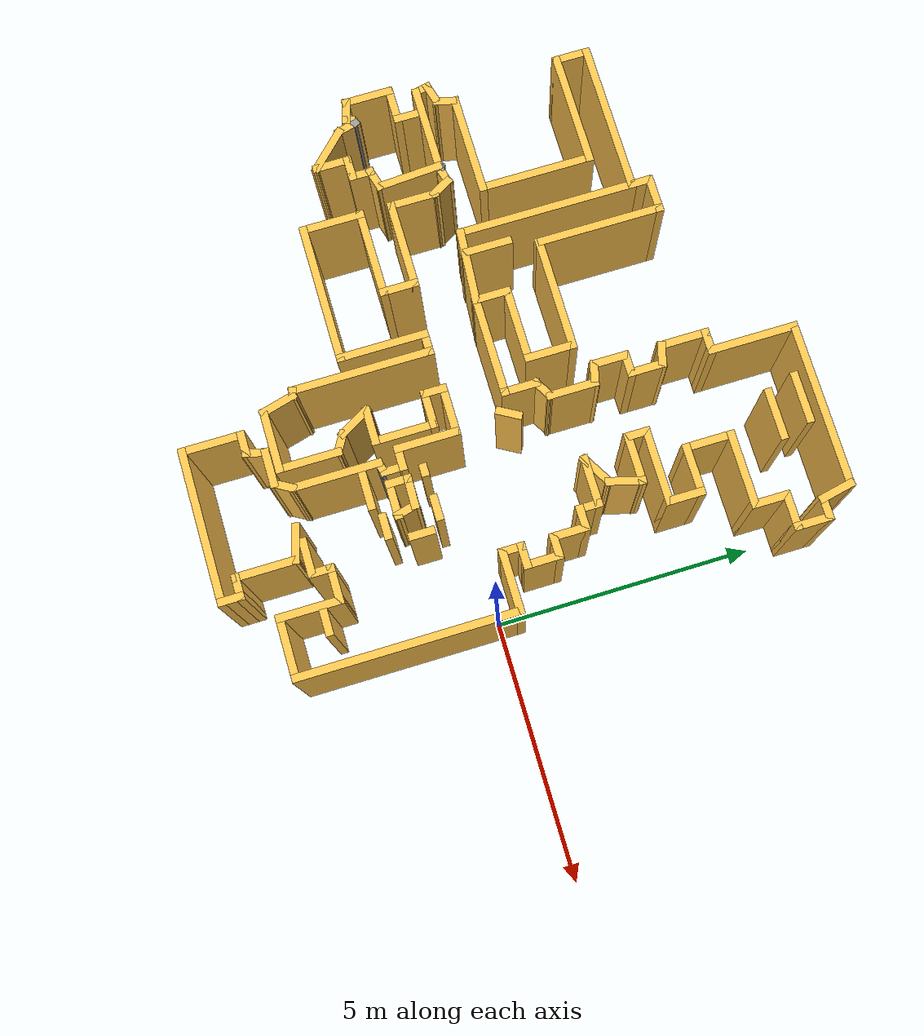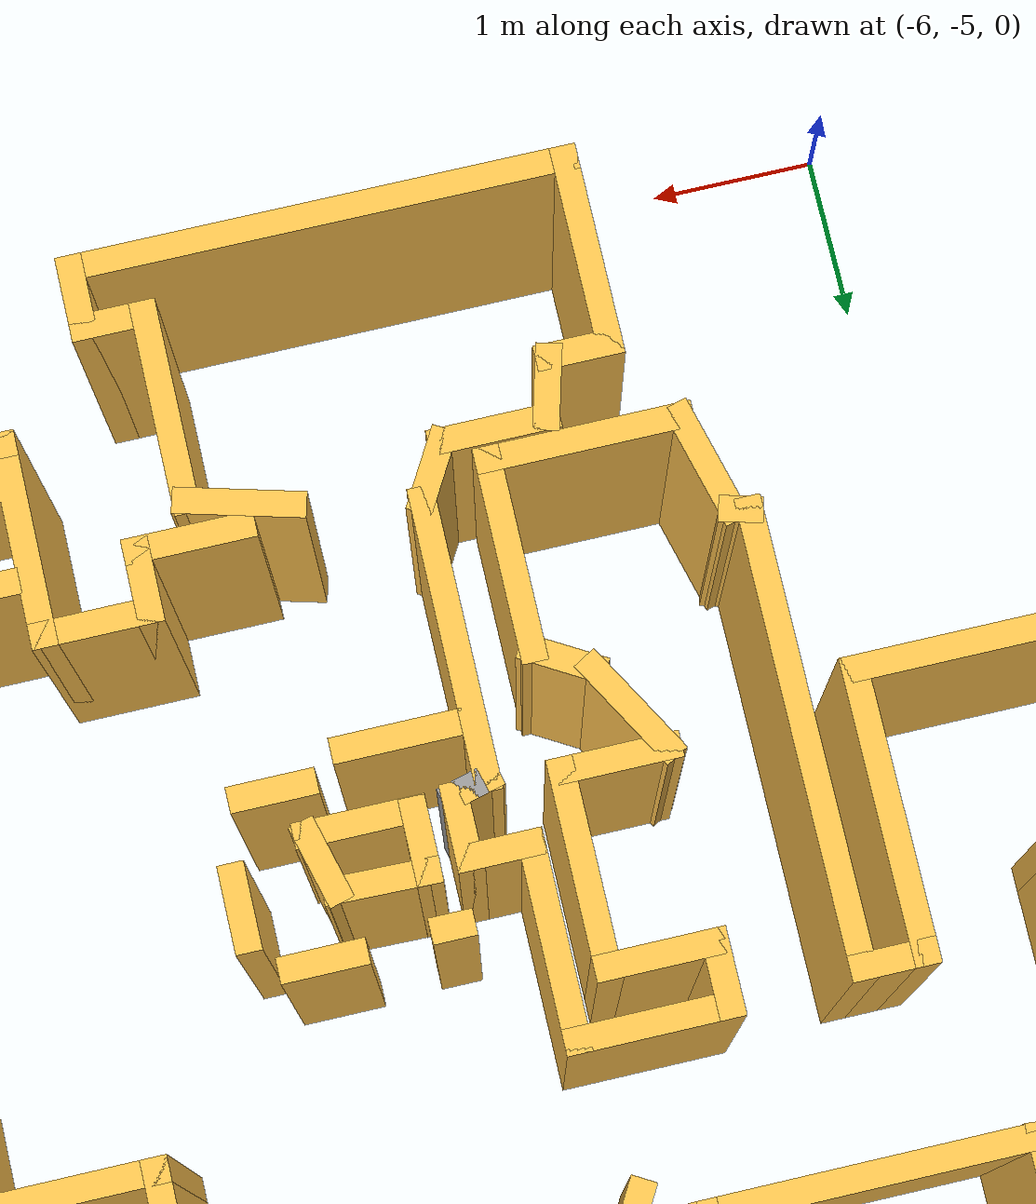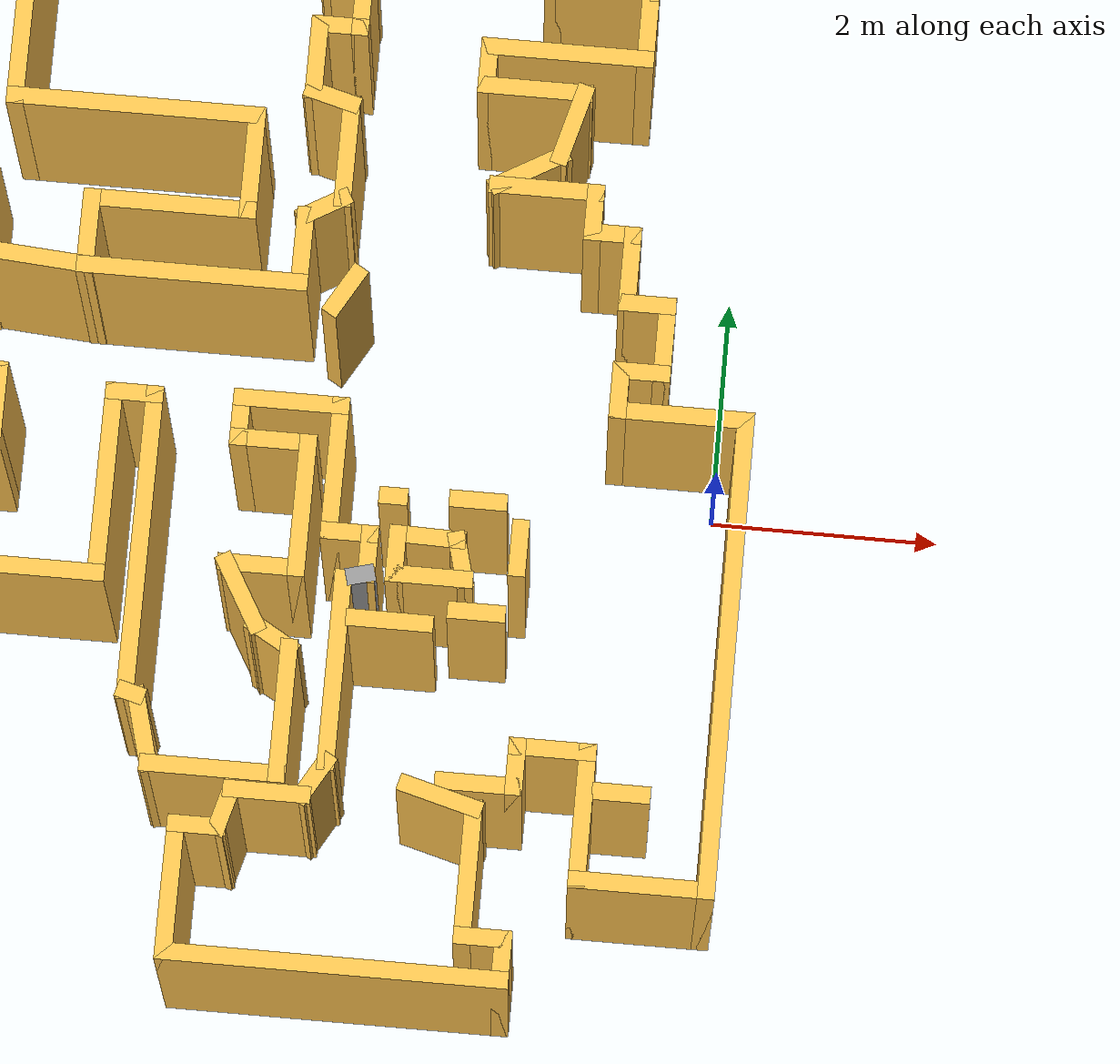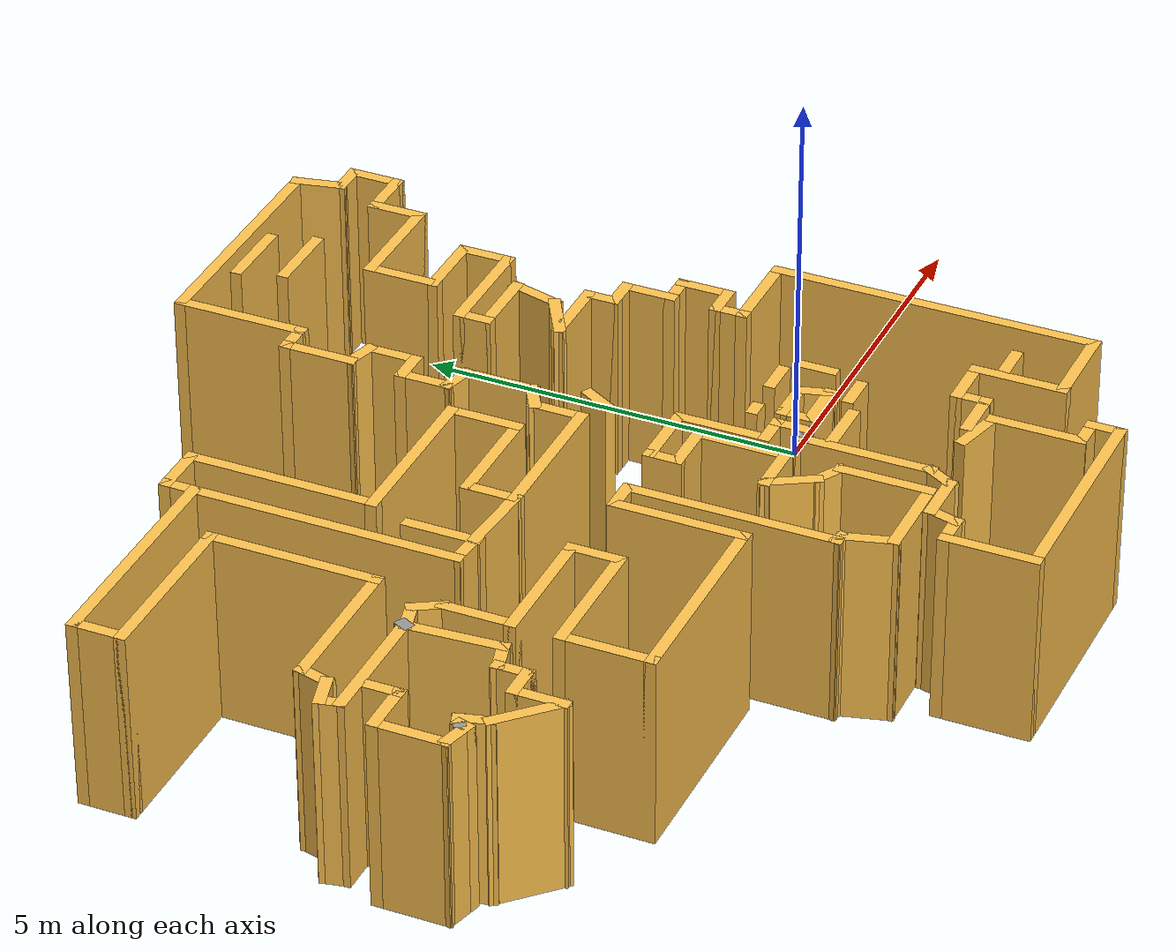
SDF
<?xml version='1.0'?>
<sdf version='1.6'>
  <model name='map_21'>
    <pose frame=''>-4.93937 1.0364 0 0 -0 0</pose>
    <link name='Wall_0'>
      <collision name='Wall_0_Collision'>
        <geometry>
          <box>
            <size>3.25 0.15 2.5</size>
          </box>
        </geometry>
        <pose frame=''>0 0 1.25 0 -0 0</pose>
      </collision>
      <visual name='Wall_0_Visual'>
        <pose frame=''>0 0 1.25 0 -0 0</pose>
        <geometry>
          <box>
            <size>3.25 0.15 2.5</size>
          </box>
        </geometry>
        <material>
          <script>
            <uri>file://media/materials/scripts/gazebo.material</uri>
            <name>Gazebo/Grey</name>
          </script>
          <ambient>1 0.764706 0.305882 1</ambient>
        </material>
        <meta>
          <layer>0</layer>
        </meta>
      </visual>
      <pose frame=''>3.10195 5.67023 0 0 -0 3.14159</pose>
    </link>
    <link name='Wall_1'>
      <collision name='Wall_1_Collision'>
        <geometry>
          <box>
            <size>1.75 0.15 2.5</size>
          </box>
        </geometry>
        <pose frame=''>0 0 1.25 0 -0 0</pose>
      </collision>
      <visual name='Wall_1_Visual'>
        <pose frame=''>0 0 1.25 0 -0 0</pose>
        <geometry>
          <box>
            <size>1.75 0.15 2.5</size>
          </box>
        </geometry>
        <material>
          <script>
            <uri>file://media/materials/scripts/gazebo.material</uri>
            <name>Gazebo/Grey</name>
          </script>
          <ambient>1 0.764706 0.305882 1</ambient>
        </material>
        <meta>
          <layer>0</layer>
        </meta>
      </visual>
      <pose frame=''>1.55195 4.87023 0 0 -0 -1.5708</pose>
    </link>
    <link name='Wall_10'>
      <collision name='Wall_10_Collision'>
        <geometry>
          <box>
            <size>0.5 0.15 2.5</size>
          </box>
        </geometry>
        <pose frame=''>0 0 1.25 0 -0 0</pose>
      </collision>
      <visual name='Wall_10_Visual'>
        <pose frame=''>0 0 1.25 0 -0 0</pose>
        <geometry>
          <box>
            <size>0.5 0.15 2.5</size>
          </box>
        </geometry>
        <material>
          <script>
            <uri>file://media/materials/scripts/gazebo.material</uri>
            <name>Gazebo/Grey</name>
          </script>
          <ambient>1 0.764706 0.305882 1</ambient>
        </material>
        <meta>
          <layer>0</layer>
        </meta>
      </visual>
      <pose frame=''>1.37654 0.901556 0 0 -0 -2.61799</pose>
    </link>
    <link name='Wall_102'>
      <collision name='Wall_102_Collision'>
        <geometry>
          <box>
            <size>3 0.15 2.5</size>
          </box>
        </geometry>
        <pose frame=''>0 0 1.25 0 -0 0</pose>
      </collision>
      <visual name='Wall_102_Visual'>
        <pose frame=''>0 0 1.25 0 -0 0</pose>
        <geometry>
          <box>
            <size>3 0.15 2.5</size>
          </box>
        </geometry>
        <material>
          <script>
            <uri>file://media/materials/scripts/gazebo.material</uri>
            <name>Gazebo/Grey</name>
          </script>
          <ambient>1 0.764706 0.305882 1</ambient>
        </material>
        <meta>
          <layer>0</layer>
        </meta>
      </visual>
      <pose frame=''>2.05029 -5.6843 0 0 -0 0</pose>
    </link>
    <link name='Wall_103'>
      <collision name='Wall_103_Collision'>
        <geometry>
          <box>
            <size>0.5 0.15 2.5</size>
          </box>
        </geometry>
        <pose frame=''>0 0 1.25 0 -0 0</pose>
      </collision>
      <visual name='Wall_103_Visual'>
        <pose frame=''>0 0 1.25 0 -0 0</pose>
        <geometry>
          <box>
            <size>0.5 0.15 2.5</size>
          </box>
        </geometry>
        <material>
          <script>
            <uri>file://media/materials/scripts/gazebo.material</uri>
            <name>Gazebo/Grey</name>
          </script>
          <ambient>1 0.764706 0.305882 1</ambient>
        </material>
        <meta>
          <layer>0</layer>
        </meta>
      </visual>
      <pose frame=''>3.47528 -5.5093 0 0 -0 1.5708</pose>
    </link>
    <link name='Wall_104'>
      <collision name='Wall_104_Collision'>
        <geometry>
          <box>
            <size>0.5 0.15 2.5</size>
          </box>
        </geometry>
        <pose frame=''>0 0 1.25 0 -0 0</pose>
      </collision>
      <visual name='Wall_104_Visual'>
        <pose frame=''>0 0 1.25 0 -0 0</pose>
        <geometry>
          <box>
            <size>0.5 0.15 2.5</size>
          </box>
        </geometry>
        <material>
          <script>
            <uri>file://media/materials/scripts/gazebo.material</uri>
            <name>Gazebo/Grey</name>
          </script>
          <ambient>1 0.764706 0.305882 1</ambient>
        </material>
        <meta>
          <layer>0</layer>
        </meta>
      </visual>
      <pose frame=''>3.30029 -5.3343 0 0 -0 3.14159</pose>
    </link>
    <link name='Wall_107'>
      <collision name='Wall_107_Collision'>
        <geometry>
          <box>
            <size>1.25 0.15 2.5</size>
          </box>
        </geometry>
        <pose frame=''>0 0 1.25 0 -0 0</pose>
      </collision>
      <visual name='Wall_107_Visual'>
        <pose frame=''>0 0 1.25 0 -0 0</pose>
        <geometry>
          <box>
            <size>1.25 0.15 2.5</size>
          </box>
        </geometry>
        <material>
          <script>
            <uri>file://media/materials/scripts/gazebo.material</uri>
            <name>Gazebo/Grey</name>
          </script>
          <ambient>1 0.764706 0.305882 1</ambient>
        </material>
        <meta>
          <layer>0</layer>
        </meta>
      </visual>
      <pose frame=''>3.12528 -4.7843 0 0 -0 1.5708</pose>
    </link>
    <link name='Wall_108'>
      <collision name='Wall_108_Collision'>
        <geometry>
          <box>
            <size>0.75 0.15 2.5</size>
          </box>
        </geometry>
        <pose frame=''>0 0 1.25 0 -0 0</pose>
      </collision>
      <visual name='Wall_108_Visual'>
        <pose frame=''>0 0 1.25 0 -0 0</pose>
        <geometry>
          <box>
            <size>0.75 0.15 2.5</size>
          </box>
        </geometry>
        <material>
          <script>
            <uri>file://media/materials/scripts/gazebo.material</uri>
            <name>Gazebo/Grey</name>
          </script>
          <ambient>1 0.764706 0.305882 1</ambient>
        </material>
        <meta>
          <layer>0</layer>
        </meta>
      </visual>
      <pose frame=''>2.83551 -4.15666 0 0 -0 2.87979</pose>
    </link>
    <link name='Wall_11'>
      <collision name='Wall_11_Collision'>
        <geometry>
          <box>
            <size>0.75 0.15 2.5</size>
          </box>
        </geometry>
        <pose frame=''>0 0 1.25 0 -0 0</pose>
      </collision>
      <visual name='Wall_11_Visual'>
        <pose frame=''>0 0 1.25 0 -0 0</pose>
        <geometry>
          <box>
            <size>0.75 0.15 2.5</size>
          </box>
        </geometry>
        <material>
          <script>
            <uri>file://media/materials/scripts/gazebo.material</uri>
            <name>Gazebo/Grey</name>
          </script>
          <ambient>1 0.764706 0.305882 1</ambient>
        </material>
        <meta>
          <layer>0</layer>
        </meta>
      </visual>
      <pose frame=''>1.22499 0.514056 0 0 -0 -1.5708</pose>
    </link>
    <link name='Wall_110'>
      <collision name='Wall_110_Collision'>
        <geometry>
          <box>
            <size>0.75 0.15 2.5</size>
          </box>
        </geometry>
        <pose frame=''>0 0 1.25 0 -0 0</pose>
      </collision>
      <visual name='Wall_110_Visual'>
        <pose frame=''>0 0 1.25 0 -0 0</pose>
        <geometry>
          <box>
            <size>0.75 0.15 2.5</size>
          </box>
        </geometry>
        <material>
          <script>
            <uri>file://media/materials/scripts/gazebo.material</uri>
            <name>Gazebo/Grey</name>
          </script>
          <ambient>1 0.764706 0.305882 1</ambient>
        </material>
        <meta>
          <layer>0</layer>
        </meta>
      </visual>
      <pose frame=''>3.14776 -4.0215 0 0 -0 0</pose>
    </link>
    <link name='Wall_114'>
      <collision name='Wall_114_Collision'>
        <geometry>
          <box>
            <size>0.5 0.15 2.5</size>
          </box>
        </geometry>
        <pose frame=''>0 0 1.25 0 -0 0</pose>
      </collision>
      <visual name='Wall_114_Visual'>
        <pose frame=''>0 0 1.25 0 -0 0</pose>
        <geometry>
          <box>
            <size>0.5 0.15 2.5</size>
          </box>
        </geometry>
        <material>
          <script>
            <uri>file://media/materials/scripts/gazebo.material</uri>
            <name>Gazebo/Grey</name>
          </script>
          <ambient>1 0.764706 0.305882 1</ambient>
        </material>
        <meta>
          <layer>0</layer>
        </meta>
      </visual>
      <pose frame=''>3.44776 -3.8465 0 0 -0 1.5708</pose>
    </link>
    <link name='Wall_115'>
      <collision name='Wall_115_Collision'>
        <geometry>
          <box>
            <size>0.75 0.15 2.5</size>
          </box>
        </geometry>
        <pose frame=''>0 0 1.25 0 -0 0</pose>
      </collision>
      <visual name='Wall_115_Visual'>
        <pose frame=''>0 0 1.25 0 -0 0</pose>
        <geometry>
          <box>
            <size>0.75 0.15 2.5</size>
          </box>
        </geometry>
        <material>
          <script>
            <uri>file://media/materials/scripts/gazebo.material</uri>
            <name>Gazebo/Grey</name>
          </script>
          <ambient>1 0.764706 0.305882 1</ambient>
        </material>
        <meta>
          <layer>0</layer>
        </meta>
      </visual>
      <pose frame=''>3.74776 -3.6715 0 0 -0 0</pose>
    </link>
    <link name='Wall_116'>
      <collision name='Wall_116_Collision'>
        <geometry>
          <box>
            <size>1.25 0.15 2.5</size>
          </box>
        </geometry>
        <pose frame=''>0 0 1.25 0 -0 0</pose>
      </collision>
      <visual name='Wall_116_Visual'>
        <pose frame=''>0 0 1.25 0 -0 0</pose>
        <geometry>
          <box>
            <size>1.25 0.15 2.5</size>
          </box>
        </geometry>
        <material>
          <script>
            <uri>file://media/materials/scripts/gazebo.material</uri>
            <name>Gazebo/Grey</name>
          </script>
          <ambient>1 0.764706 0.305882 1</ambient>
        </material>
        <meta>
          <layer>0</layer>
        </meta>
      </visual>
      <pose frame=''>4.04776 -4.2215 0 0 -0 -1.5708</pose>
    </link>
    <link name='Wall_117'>
      <collision name='Wall_117_Collision'>
        <geometry>
          <box>
            <size>1.25 0.15 2.5</size>
          </box>
        </geometry>
        <pose frame=''>0 0 1.25 0 -0 0</pose>
      </collision>
      <visual name='Wall_117_Visual'>
        <pose frame=''>0 0 1.25 0 -0 0</pose>
        <geometry>
          <box>
            <size>1.25 0.15 2.5</size>
          </box>
        </geometry>
        <material>
          <script>
            <uri>file://media/materials/scripts/gazebo.material</uri>
            <name>Gazebo/Grey</name>
          </script>
          <ambient>1 0.764706 0.305882 1</ambient>
        </material>
        <meta>
          <layer>0</layer>
        </meta>
      </visual>
      <pose frame=''>4.59776 -4.7715 0 0 -0 0</pose>
    </link>
    <link name='Wall_118'>
      <collision name='Wall_118_Collision'>
        <geometry>
          <box>
            <size>4.25 0.15 2.5</size>
          </box>
        </geometry>
        <pose frame=''>0 0 1.25 0 -0 0</pose>
      </collision>
      <visual name='Wall_118_Visual'>
        <pose frame=''>0 0 1.25 0 -0 0</pose>
        <geometry>
          <box>
            <size>4.25 0.15 2.5</size>
          </box>
        </geometry>
        <material>
          <script>
            <uri>file://media/materials/scripts/gazebo.material</uri>
            <name>Gazebo/Grey</name>
          </script>
          <ambient>1 0.764706 0.305882 1</ambient>
        </material>
        <meta>
          <layer>0</layer>
        </meta>
      </visual>
      <pose frame=''>5.14776 -2.7215 0 0 -0 1.5708</pose>
    </link>
    <link name='Wall_119'>
      <collision name='Wall_119_Collision'>
        <geometry>
          <box>
            <size>1.25 0.15 2.5</size>
          </box>
        </geometry>
        <pose frame=''>0 0 1.25 0 -0 0</pose>
      </collision>
      <visual name='Wall_119_Visual'>
        <pose frame=''>0 0 1.25 0 -0 0</pose>
        <geometry>
          <box>
            <size>1.25 0.15 2.5</size>
          </box>
        </geometry>
        <material>
          <script>
            <uri>file://media/materials/scripts/gazebo.material</uri>
            <name>Gazebo/Grey</name>
          </script>
          <ambient>1 0.764706 0.305882 1</ambient>
        </material>
        <meta>
          <layer>0</layer>
        </meta>
      </visual>
      <pose frame=''>4.59776 -0.671496 0 0 -0 3.14159</pose>
    </link>
    <link name='Wall_12'>
      <collision name='Wall_12_Collision'>
        <geometry>
          <box>
            <size>2 0.15 2.5</size>
          </box>
        </geometry>
        <pose frame=''>0 0 1.25 0 -0 0</pose>
      </collision>
      <visual name='Wall_12_Visual'>
        <pose frame=''>0 0 1.25 0 -0 0</pose>
        <geometry>
          <box>
            <size>2 0.15 2.5</size>
          </box>
        </geometry>
        <material>
          <script>
            <uri>file://media/materials/scripts/gazebo.material</uri>
            <name>Gazebo/Grey</name>
          </script>
          <ambient>1 0.764706 0.305882 1</ambient>
        </material>
        <meta>
          <layer>0</layer>
        </meta>
      </visual>
      <pose frame=''>0.299987 0.214056 0 0 -0 3.14159</pose>
    </link>
    <link name='Wall_122'>
      <collision name='Wall_122_Collision'>
        <geometry>
          <box>
            <size>0.5 0.15 2.5</size>
          </box>
        </geometry>
        <pose frame=''>0 0 1.25 0 -0 0</pose>
      </collision>
      <visual name='Wall_122_Visual'>
        <pose frame=''>0 0 1.25 0 -0 0</pose>
        <geometry>
          <box>
            <size>0.5 0.15 2.5</size>
          </box>
        </geometry>
        <material>
          <script>
            <uri>file://media/materials/scripts/gazebo.material</uri>
            <name>Gazebo/Grey</name>
          </script>
          <ambient>1 0.764706 0.305882 1</ambient>
        </material>
        <meta>
          <layer>0</layer>
        </meta>
      </visual>
      <pose frame=''>4.04776 -0.496496 0 0 -0 1.5708</pose>
    </link>
    <link name='Wall_123'>
      <collision name='Wall_123_Collision'>
        <geometry>
          <box>
            <size>0.5 0.15 2.5</size>
          </box>
        </geometry>
        <pose frame=''>0 0 1.25 0 -0 0</pose>
      </collision>
      <visual name='Wall_123_Visual'>
        <pose frame=''>0 0 1.25 0 -0 0</pose>
        <geometry>
          <box>
            <size>0.5 0.15 2.5</size>
          </box>
        </geometry>
        <material>
          <script>
            <uri>file://media/materials/scripts/gazebo.material</uri>
            <name>Gazebo/Grey</name>
          </script>
          <ambient>1 0.764706 0.305882 1</ambient>
        </material>
        <meta>
          <layer>0</layer>
        </meta>
      </visual>
      <pose frame=''>4.22276 -0.321496 0 0 -0 0</pose>
    </link>
    <link name='Wall_124'>
      <collision name='Wall_124_Collision'>
        <geometry>
          <box>
            <size>0.75 0.15 2.5</size>
          </box>
        </geometry>
        <pose frame=''>0 0 1.25 0 -0 0</pose>
      </collision>
      <visual name='Wall_124_Visual'>
        <pose frame=''>0 0 1.25 0 -0 0</pose>
        <geometry>
          <box>
            <size>0.75 0.15 2.5</size>
          </box>
        </geometry>
        <material>
          <script>
            <uri>file://media/materials/scripts/gazebo.material</uri>
            <name>Gazebo/Grey</name>
          </script>
          <ambient>1 0.764706 0.305882 1</ambient>
        </material>
        <meta>
          <layer>0</layer>
        </meta>
      </visual>
      <pose frame=''>4.39776 -0.021496 0 0 -0 1.5708</pose>
    </link>
    <link name='Wall_125'>
      <collision name='Wall_125_Collision'>
        <geometry>
          <box>
            <size>0.5 0.15 2.5</size>
          </box>
        </geometry>
        <pose frame=''>0 0 1.25 0 -0 0</pose>
      </collision>
      <visual name='Wall_125_Visual'>
        <pose frame=''>0 0 1.25 0 -0 0</pose>
        <geometry>
          <box>
            <size>0.5 0.15 2.5</size>
          </box>
        </geometry>
        <material>
          <script>
            <uri>file://media/materials/scripts/gazebo.material</uri>
            <name>Gazebo/Grey</name>
          </script>
          <ambient>1 0.764706 0.305882 1</ambient>
        </material>
        <meta>
          <layer>0</layer>
        </meta>
      </visual>
      <pose frame=''>4.22276 0.278504 0 0 -0 3.14159</pose>
    </link>
    <link name='Wall_126'>
      <collision name='Wall_126_Collision'>
        <geometry>
          <box>
            <size>0.75 0.15 2.5</size>
          </box>
        </geometry>
        <pose frame=''>0 0 1.25 0 -0 0</pose>
      </collision>
      <visual name='Wall_126_Visual'>
        <pose frame=''>0 0 1.25 0 -0 0</pose>
        <geometry>
          <box>
            <size>0.75 0.15 2.5</size>
          </box>
        </geometry>
        <material>
          <script>
            <uri>file://media/materials/scripts/gazebo.material</uri>
            <name>Gazebo/Grey</name>
          </script>
          <ambient>1 0.764706 0.305882 1</ambient>
        </material>
        <meta>
          <layer>0</layer>
        </meta>
      </visual>
      <pose frame=''>4.04776 0.578504 0 0 -0 1.5708</pose>
    </link>
    <link name='Wall_127'>
      <collision name='Wall_127_Collision'>
        <geometry>
          <box>
            <size>0.5 0.15 2.5</size>
          </box>
        </geometry>
        <pose frame=''>0 0 1.25 0 -0 0</pose>
      </collision>
      <visual name='Wall_127_Visual'>
        <pose frame=''>0 0 1.25 0 -0 0</pose>
        <geometry>
          <box>
            <size>0.5 0.15 2.5</size>
          </box>
        </geometry>
        <material>
          <script>
            <uri>file://media/materials/scripts/gazebo.material</uri>
            <name>Gazebo/Grey</name>
          </script>
          <ambient>1 0.764706 0.305882 1</ambient>
        </material>
        <meta>
          <layer>0</layer>
        </meta>
      </visual>
      <pose frame=''>3.87276 0.878504 0 0 -0 3.14159</pose>
    </link>
    <link name='Wall_128'>
      <collision name='Wall_128_Collision'>
        <geometry>
          <box>
            <size>0.5 0.15 2.5</size>
          </box>
        </geometry>
        <pose frame=''>0 0 1.25 0 -0 0</pose>
      </collision>
      <visual name='Wall_128_Visual'>
        <pose frame=''>0 0 1.25 0 -0 0</pose>
        <geometry>
          <box>
            <size>0.5 0.15 2.5</size>
          </box>
        </geometry>
        <material>
          <script>
            <uri>file://media/materials/scripts/gazebo.material</uri>
            <name>Gazebo/Grey</name>
          </script>
          <ambient>1 0.764706 0.305882 1</ambient>
        </material>
        <meta>
          <layer>0</layer>
        </meta>
      </visual>
      <pose frame=''>3.69776 1.0535 0 0 -0 1.5708</pose>
    </link>
    <link name='Wall_129'>
      <collision name='Wall_129_Collision'>
        <geometry>
          <box>
            <size>1 0.15 2.5</size>
          </box>
        </geometry>
        <pose frame=''>0 0 1.25 0 -0 0</pose>
      </collision>
      <visual name='Wall_129_Visual'>
        <pose frame=''>0 0 1.25 0 -0 0</pose>
        <geometry>
          <box>
            <size>1 0.15 2.5</size>
          </box>
        </geometry>
        <material>
          <script>
            <uri>file://media/materials/scripts/gazebo.material</uri>
            <name>Gazebo/Grey</name>
          </script>
          <ambient>1 0.764706 0.305882 1</ambient>
        </material>
        <meta>
          <layer>0</layer>
        </meta>
      </visual>
      <pose frame=''>3.27276 1.2285 0 0 -0 3.14159</pose>
    </link>
    <link name='Wall_13'>
      <collision name='Wall_13_Collision'>
        <geometry>
          <box>
            <size>0.75 0.15 2.5</size>
          </box>
        </geometry>
        <pose frame=''>0 0 1.25 0 -0 0</pose>
      </collision>
      <visual name='Wall_13_Visual'>
        <pose frame=''>0 0 1.25 0 -0 0</pose>
        <geometry>
          <box>
            <size>0.75 0.15 2.5</size>
          </box>
        </geometry>
        <material>
          <script>
            <uri>file://media/materials/scripts/gazebo.material</uri>
            <name>Gazebo/Grey</name>
          </script>
          <ambient>1 0.764706 0.305882 1</ambient>
        </material>
        <meta>
          <layer>0</layer>
        </meta>
      </visual>
      <pose frame=''>-0.625014 0.514056 0 0 -0 1.5708</pose>
    </link>
    <link name='Wall_130'>
      <collision name='Wall_130_Collision'>
        <geometry>
          <box>
            <size>0.75 0.15 2.5</size>
          </box>
        </geometry>
        <pose frame=''>0 0 1.25 0 -0 0</pose>
      </collision>
      <visual name='Wall_130_Visual'>
        <pose frame=''>0 0 1.25 0 -0 0</pose>
        <geometry>
          <box>
            <size>0.75 0.15 2.5</size>
          </box>
        </geometry>
        <material>
          <script>
            <uri>file://media/materials/scripts/gazebo.material</uri>
            <name>Gazebo/Grey</name>
          </script>
          <ambient>1 0.764706 0.305882 1</ambient>
        </material>
        <meta>
          <layer>0</layer>
        </meta>
      </visual>
      <pose frame=''>3.10757 1.3785 0 0 -0 0.523599</pose>
    </link>
    <link name='Wall_131'>
      <collision name='Wall_131_Collision'>
        <geometry>
          <box>
            <size>0.75 0.15 2.5</size>
          </box>
        </geometry>
        <pose frame=''>0 0 1.25 0 -0 0</pose>
      </collision>
      <visual name='Wall_131_Visual'>
        <pose frame=''>0 0 1.25 0 -0 0</pose>
        <geometry>
          <box>
            <size>0.75 0.15 2.5</size>
          </box>
        </geometry>
        <material>
          <script>
            <uri>file://media/materials/scripts/gazebo.material</uri>
            <name>Gazebo/Grey</name>
          </script>
          <ambient>1 0.764706 0.305882 1</ambient>
        </material>
        <meta>
          <layer>0</layer>
        </meta>
      </visual>
      <pose frame=''>3.44502 1.81828 0 0 -0 1.309</pose>
    </link>
    <link name='Wall_132'>
      <collision name='Wall_132_Collision'>
        <geometry>
          <box>
            <size>1 0.15 2.5</size>
          </box>
        </geometry>
        <pose frame=''>0 0 1.25 0 -0 0</pose>
      </collision>
      <visual name='Wall_132_Visual'>
        <pose frame=''>0 0 1.25 0 -0 0</pose>
        <geometry>
          <box>
            <size>1 0.15 2.5</size>
          </box>
        </geometry>
        <material>
          <script>
            <uri>file://media/materials/scripts/gazebo.material</uri>
            <name>Gazebo/Grey</name>
          </script>
          <ambient>1 0.764706 0.305882 1</ambient>
        </material>
        <meta>
          <layer>0</layer>
        </meta>
      </visual>
      <pose frame=''>3.09767 2.10806 0 0 -0 3.14159</pose>
    </link>
    <link name='Wall_133'>
      <collision name='Wall_133_Collision'>
        <geometry>
          <box>
            <size>0.5 0.15 2.5</size>
          </box>
        </geometry>
        <pose frame=''>0 0 1.25 0 -0 0</pose>
      </collision>
      <visual name='Wall_133_Visual'>
        <pose frame=''>0 0 1.25 0 -0 0</pose>
        <geometry>
          <box>
            <size>0.5 0.15 2.5</size>
          </box>
        </geometry>
        <material>
          <script>
            <uri>file://media/materials/scripts/gazebo.material</uri>
            <name>Gazebo/Grey</name>
          </script>
          <ambient>1 0.764706 0.305882 1</ambient>
        </material>
        <meta>
          <layer>0</layer>
        </meta>
      </visual>
      <pose frame=''>2.67267 2.28306 0 0 -0 1.5708</pose>
    </link>
    <link name='Wall_134'>
      <collision name='Wall_134_Collision'>
        <geometry>
          <box>
            <size>1.5 0.15 2.5</size>
          </box>
        </geometry>
        <pose frame=''>0 0 1.25 0 -0 0</pose>
      </collision>
      <visual name='Wall_134_Visual'>
        <pose frame=''>0 0 1.25 0 -0 0</pose>
        <geometry>
          <box>
            <size>1.5 0.15 2.5</size>
          </box>
        </geometry>
        <material>
          <script>
            <uri>file://media/materials/scripts/gazebo.material</uri>
            <name>Gazebo/Grey</name>
          </script>
          <ambient>1 0.764706 0.305882 1</ambient>
        </material>
        <meta>
          <layer>0</layer>
        </meta>
      </visual>
      <pose frame=''>3.34767 2.45806 0 0 -0 0</pose>
    </link>
    <link name='Wall_135'>
      <collision name='Wall_135_Collision'>
        <geometry>
          <box>
            <size>0.75 0.15 2.5</size>
          </box>
        </geometry>
        <pose frame=''>0 0 1.25 0 -0 0</pose>
      </collision>
      <visual name='Wall_135_Visual'>
        <pose frame=''>0 0 1.25 0 -0 0</pose>
        <geometry>
          <box>
            <size>0.75 0.15 2.5</size>
          </box>
        </geometry>
        <material>
          <script>
            <uri>file://media/materials/scripts/gazebo.material</uri>
            <name>Gazebo/Grey</name>
          </script>
          <ambient>1 0.764706 0.305882 1</ambient>
        </material>
        <meta>
          <layer>0</layer>
        </meta>
      </visual>
      <pose frame=''>4.02267 2.75806 0 0 -0 1.5708</pose>
    </link>
    <link name='Wall_136'>
      <collision name='Wall_136_Collision'>
        <geometry>
          <box>
            <size>1 0.15 2.5</size>
          </box>
        </geometry>
        <pose frame=''>0 0 1.25 0 -0 0</pose>
      </collision>
      <visual name='Wall_136_Visual'>
        <pose frame=''>0 0 1.25 0 -0 0</pose>
        <geometry>
          <box>
            <size>1 0.15 2.5</size>
          </box>
        </geometry>
        <material>
          <script>
            <uri>file://media/materials/scripts/gazebo.material</uri>
            <name>Gazebo/Grey</name>
          </script>
          <ambient>1 0.764706 0.305882 1</ambient>
        </material>
        <meta>
          <layer>0</layer>
        </meta>
      </visual>
      <pose frame=''>3.59767 3.05806 0 0 -0 3.14159</pose>
    </link>
    <link name='Wall_137'>
      <collision name='Wall_137_Collision'>
        <geometry>
          <box>
            <size>1 0.15 2.5</size>
          </box>
        </geometry>
        <pose frame=''>0 0 1.25 0 -0 0</pose>
      </collision>
      <visual name='Wall_137_Visual'>
        <pose frame=''>0 0 1.25 0 -0 0</pose>
        <geometry>
          <box>
            <size>1 0.15 2.5</size>
          </box>
        </geometry>
        <material>
          <script>
            <uri>file://media/materials/scripts/gazebo.material</uri>
            <name>Gazebo/Grey</name>
          </script>
          <ambient>1 0.764706 0.305882 1</ambient>
        </material>
        <meta>
          <layer>0</layer>
        </meta>
      </visual>
      <pose frame=''>3.17267 3.48306 0 0 -0 1.5708</pose>
    </link>
    <link name='Wall_138'>
      <collision name='Wall_138_Collision'>
        <geometry>
          <box>
            <size>1.5 0.15 2.5</size>
          </box>
        </geometry>
        <pose frame=''>0 0 1.25 0 -0 0</pose>
      </collision>
      <visual name='Wall_138_Visual'>
        <pose frame=''>0 0 1.25 0 -0 0</pose>
        <geometry>
          <box>
            <size>1.5 0.15 2.5</size>
          </box>
        </geometry>
        <material>
          <script>
            <uri>file://media/materials/scripts/gazebo.material</uri>
            <name>Gazebo/Grey</name>
          </script>
          <ambient>1 0.764706 0.305882 1</ambient>
        </material>
        <meta>
          <layer>0</layer>
        </meta>
      </visual>
      <pose frame=''>3.84767 3.90806 0 0 -0 0</pose>
    </link>
    <link name='Wall_139'>
      <collision name='Wall_139_Collision'>
        <geometry>
          <box>
            <size>0.75 0.15 2.5</size>
          </box>
        </geometry>
        <pose frame=''>0 0 1.25 0 -0 0</pose>
      </collision>
      <visual name='Wall_139_Visual'>
        <pose frame=''>0 0 1.25 0 -0 0</pose>
        <geometry>
          <box>
            <size>0.75 0.15 2.5</size>
          </box>
        </geometry>
        <material>
          <script>
            <uri>file://media/materials/scripts/gazebo.material</uri>
            <name>Gazebo/Grey</name>
          </script>
          <ambient>1 0.764706 0.305882 1</ambient>
        </material>
        <meta>
          <layer>0</layer>
        </meta>
      </visual>
      <pose frame=''>4.52267 4.20806 0 0 -0 1.5708</pose>
    </link>
    <link name='Wall_14'>
      <collision name='Wall_14_Collision'>
        <geometry>
          <box>
            <size>1.5 0.15 2.5</size>
          </box>
        </geometry>
        <pose frame=''>0 0 1.25 0 -0 0</pose>
      </collision>
      <visual name='Wall_14_Visual'>
        <pose frame=''>0 0 1.25 0 -0 0</pose>
        <geometry>
          <box>
            <size>1.5 0.15 2.5</size>
          </box>
        </geometry>
        <material>
          <script>
            <uri>file://media/materials/scripts/gazebo.material</uri>
            <name>Gazebo/Grey</name>
          </script>
          <ambient>1 0.764706 0.305882 1</ambient>
        </material>
        <meta>
          <layer>0</layer>
        </meta>
      </visual>
      <pose frame=''>0.049987 0.814056 0 0 -0 0</pose>
    </link>
    <link name='Wall_140'>
      <collision name='Wall_140_Collision'>
        <geometry>
          <box>
            <size>0.75 0.15 2.5</size>
          </box>
        </geometry>
        <pose frame=''>0 0 1.25 0 -0 0</pose>
      </collision>
      <visual name='Wall_140_Visual'>
        <pose frame=''>0 0 1.25 0 -0 0</pose>
        <geometry>
          <box>
            <size>0.75 0.15 2.5</size>
          </box>
        </geometry>
        <material>
          <script>
            <uri>file://media/materials/scripts/gazebo.material</uri>
            <name>Gazebo/Grey</name>
          </script>
          <ambient>1 0.764706 0.305882 1</ambient>
        </material>
        <meta>
          <layer>0</layer>
        </meta>
      </visual>
      <pose frame=''>4.82267 4.50806 0 0 -0 0</pose>
    </link>
    <link name='Wall_141'>
      <collision name='Wall_141_Collision'>
        <geometry>
          <box>
            <size>0.75 0.15 2.5</size>
          </box>
        </geometry>
        <pose frame=''>0 0 1.25 0 -0 0</pose>
      </collision>
      <visual name='Wall_141_Visual'>
        <pose frame=''>0 0 1.25 0 -0 0</pose>
        <geometry>
          <box>
            <size>0.75 0.15 2.5</size>
          </box>
        </geometry>
        <material>
          <script>
            <uri>file://media/materials/scripts/gazebo.material</uri>
            <name>Gazebo/Grey</name>
          </script>
          <ambient>1 0.764706 0.305882 1</ambient>
        </material>
        <meta>
          <layer>0</layer>
        </meta>
      </visual>
      <pose frame=''>5.12267 4.80806 0 0 -0 1.5708</pose>
    </link>
    <link name='Wall_142'>
      <collision name='Wall_142_Collision'>
        <geometry>
          <box>
            <size>0.5 0.15 2.5</size>
          </box>
        </geometry>
        <pose frame=''>0 0 1.25 0 -0 0</pose>
      </collision>
      <visual name='Wall_142_Visual'>
        <pose frame=''>0 0 1.25 0 -0 0</pose>
        <geometry>
          <box>
            <size>0.5 0.15 2.5</size>
          </box>
        </geometry>
        <material>
          <script>
            <uri>file://media/materials/scripts/gazebo.material</uri>
            <name>Gazebo/Grey</name>
          </script>
          <ambient>1 0.764706 0.305882 1</ambient>
        </material>
        <meta>
          <layer>0</layer>
        </meta>
      </visual>
      <pose frame=''>4.94767 5.10806 0 0 -0 3.14159</pose>
    </link>
    <link name='Wall_143'>
      <collision name='Wall_143_Collision'>
        <geometry>
          <box>
            <size>0.724985 0.15 2.5</size>
          </box>
        </geometry>
        <pose frame=''>0 0 1.25 0 -0 0</pose>
      </collision>
      <visual name='Wall_143_Visual'>
        <pose frame=''>0 0 1.25 0 -0 0</pose>
        <geometry>
          <box>
            <size>0.724985 0.15 2.5</size>
          </box>
        </geometry>
        <material>
          <script>
            <uri>file://media/materials/scripts/gazebo.material</uri>
            <name>Gazebo/Grey</name>
          </script>
          <ambient>1 0.764706 0.305882 1</ambient>
        </material>
        <meta>
          <layer>0</layer>
        </meta>
      </visual>
      <pose frame=''>4.71231 5.38914 0 0 -0 1.78232</pose>
    </link>
    <link name='Wall_145'>
      <collision name='Wall_145_Collision'>
        <geometry>
          <box>
            <size>1 0.15 2.5</size>
          </box>
        </geometry>
        <pose frame=''>0 0 1.25 0 -0 0</pose>
      </collision>
      <visual name='Wall_145_Visual'>
        <pose frame=''>0 0 1.25 0 -0 0</pose>
        <geometry>
          <box>
            <size>1 0.15 2.5</size>
          </box>
        </geometry>
        <material>
          <script>
            <uri>file://media/materials/scripts/gazebo.material</uri>
            <name>Gazebo/Grey</name>
          </script>
          <ambient>1 0.764706 0.305882 1</ambient>
        </material>
        <meta>
          <layer>0</layer>
        </meta>
      </visual>
      <pose frame=''>2.87954 5.36953 0 0 -0 0</pose>
    </link>
    <link name='Wall_147'>
      <collision name='Wall_147_Collision'>
        <geometry>
          <box>
            <size>1 0.15 2.5</size>
          </box>
        </geometry>
        <pose frame=''>0 0 1.25 0 -0 0</pose>
      </collision>
      <visual name='Wall_147_Visual'>
        <pose frame=''>0 0 1.25 0 -0 0</pose>
        <geometry>
          <box>
            <size>1 0.15 2.5</size>
          </box>
        </geometry>
        <material>
          <script>
            <uri>file://media/materials/scripts/gazebo.material</uri>
            <name>Gazebo/Grey</name>
          </script>
          <ambient>1 0.764706 0.305882 1</ambient>
        </material>
        <meta>
          <layer>0</layer>
        </meta>
      </visual>
      <pose frame=''>3.04145 4.8144 0 0 -0 0</pose>
    </link>
    <link name='Wall_15'>
      <collision name='Wall_15_Collision'>
        <geometry>
          <box>
            <size>1 0.15 2.5</size>
          </box>
        </geometry>
        <pose frame=''>0 0 1.25 0 -0 0</pose>
      </collision>
      <visual name='Wall_15_Visual'>
        <pose frame=''>0 0 1.25 0 -0 0</pose>
        <geometry>
          <box>
            <size>1 0.15 2.5</size>
          </box>
        </geometry>
        <material>
          <script>
            <uri>file://media/materials/scripts/gazebo.material</uri>
            <name>Gazebo/Grey</name>
          </script>
          <ambient>1 0.764706 0.305882 1</ambient>
        </material>
        <meta>
          <layer>0</layer>
        </meta>
      </visual>
      <pose frame=''>0.724986 1.23906 0 0 -0 1.5708</pose>
    </link>
    <link name='Wall_150'>
      <collision name='Wall_150_Collision'>
        <geometry>
          <box>
            <size>0.5 0.15 2.5</size>
          </box>
        </geometry>
        <pose frame=''>0 0 1.25 0 -0 0</pose>
      </collision>
      <visual name='Wall_150_Visual'>
        <pose frame=''>0 0 1.25 0 -0 0</pose>
        <geometry>
          <box>
            <size>0.5 0.15 2.5</size>
          </box>
        </geometry>
        <material>
          <script>
            <uri>file://media/materials/scripts/gazebo.material</uri>
            <name>Gazebo/Grey</name>
          </script>
          <ambient>1 0.764706 0.305882 1</ambient>
        </material>
        <meta>
          <layer>0</layer>
        </meta>
      </visual>
      <pose frame=''>1.62686 0.175504 0 0 -0 -2.0944</pose>
    </link>
    <link name='Wall_155'>
      <collision name='Wall_155_Collision'>
        <geometry>
          <box>
            <size>3.5 0.15 2.5</size>
          </box>
        </geometry>
        <pose frame=''>0 0 1.25 0 -0 0</pose>
      </collision>
      <visual name='Wall_155_Visual'>
        <pose frame=''>0 0 1.25 0 -0 0</pose>
        <geometry>
          <box>
            <size>3.5 0.15 2.5</size>
          </box>
        </geometry>
        <material>
          <script>
            <uri>file://media/materials/scripts/gazebo.material</uri>
            <name>Gazebo/Grey</name>
          </script>
          <ambient>1 0.764706 0.305882 1</ambient>
        </material>
        <meta>
          <layer>0</layer>
        </meta>
      </visual>
      <pose frame=''>-1.97501 1.98906 0 0 -0 -1.5708</pose>
    </link>
    <link name='Wall_156'>
      <collision name='Wall_156_Collision'>
        <geometry>
          <box>
            <size>1.5037 0.15 2.5</size>
          </box>
        </geometry>
        <pose frame=''>0 0 1.25 0 -0 0</pose>
      </collision>
      <visual name='Wall_156_Visual'>
        <pose frame=''>0 0 1.25 0 -0 0</pose>
        <geometry>
          <box>
            <size>1.5037 0.15 2.5</size>
          </box>
        </geometry>
        <material>
          <script>
            <uri>file://media/materials/scripts/gazebo.material</uri>
            <name>Gazebo/Grey</name>
          </script>
          <ambient>1 0.764706 0.305882 1</ambient>
        </material>
        <meta>
          <layer>0</layer>
        </meta>
      </visual>
      <pose frame=''>-1.30001 0.264056 0 0 -0 -0.073939</pose>
    </link>
    <link name='Wall_158'>
      <collision name='Wall_158_Collision'>
        <geometry>
          <box>
            <size>1 0.15 2.5</size>
          </box>
        </geometry>
        <pose frame=''>0 0 1.25 0 -0 0</pose>
      </collision>
      <visual name='Wall_158_Visual'>
        <pose frame=''>0 0 1.25 0 -0 0</pose>
        <geometry>
          <box>
            <size>1 0.15 2.5</size>
          </box>
        </geometry>
        <material>
          <script>
            <uri>file://media/materials/scripts/gazebo.material</uri>
            <name>Gazebo/Grey</name>
          </script>
          <ambient>1 0.764706 0.305882 1</ambient>
        </material>
        <meta>
          <layer>0</layer>
        </meta>
      </visual>
      <pose frame=''>-1.57019 0.688499 0 0 -0 -1.5708</pose>
    </link>
    <link name='Wall_16'>
      <collision name='Wall_16_Collision'>
        <geometry>
          <box>
            <size>2.25 0.15 2.5</size>
          </box>
        </geometry>
        <pose frame=''>0 0 1.25 0 -0 0</pose>
      </collision>
      <visual name='Wall_16_Visual'>
        <pose frame=''>0 0 1.25 0 -0 0</pose>
        <geometry>
          <box>
            <size>2.25 0.15 2.5</size>
          </box>
        </geometry>
        <material>
          <script>
            <uri>file://media/materials/scripts/gazebo.material</uri>
            <name>Gazebo/Grey</name>
          </script>
          <ambient>1 0.764706 0.305882 1</ambient>
        </material>
        <meta>
          <layer>0</layer>
        </meta>
      </visual>
      <pose frame=''>-0.325013 1.66406 0 0 -0 3.14159</pose>
    </link>
    <link name='Wall_161'>
      <collision name='Wall_161_Collision'>
        <geometry>
          <box>
            <size>0.75 0.15 2.5</size>
          </box>
        </geometry>
        <pose frame=''>0 0 1.25 0 -0 0</pose>
      </collision>
      <visual name='Wall_161_Visual'>
        <pose frame=''>0 0 1.25 0 -0 0</pose>
        <geometry>
          <box>
            <size>0.75 0.15 2.5</size>
          </box>
        </geometry>
        <material>
          <script>
            <uri>file://media/materials/scripts/gazebo.material</uri>
            <name>Gazebo/Grey</name>
          </script>
          <ambient>1 0.764706 0.305882 1</ambient>
        </material>
        <meta>
          <layer>0</layer>
        </meta>
      </visual>
      <pose frame=''>2.2688 -2.67992 0 0 -0 0</pose>
    </link>
    <link name='Wall_163'>
      <collision name='Wall_163_Collision'>
        <geometry>
          <box>
            <size>0.5 0.15 2.5</size>
          </box>
        </geometry>
        <pose frame=''>0 0 1.25 0 -0 0</pose>
      </collision>
      <visual name='Wall_163_Visual'>
        <pose frame=''>0 0 1.25 0 -0 0</pose>
        <geometry>
          <box>
            <size>0.5 0.15 2.5</size>
          </box>
        </geometry>
        <material>
          <script>
            <uri>file://media/materials/scripts/gazebo.material</uri>
            <name>Gazebo/Grey</name>
          </script>
          <ambient>1 0.764706 0.305882 1</ambient>
        </material>
        <meta>
          <layer>0</layer>
        </meta>
      </visual>
      <pose frame=''>2.99963 -2.54114 0 0 -0 0</pose>
    </link>
    <link name='Wall_165'>
      <collision name='Wall_165_Collision'>
        <geometry>
          <box>
            <size>0.5 0.15 2.5</size>
          </box>
        </geometry>
        <pose frame=''>0 0 1.25 0 -0 0</pose>
      </collision>
      <visual name='Wall_165_Visual'>
        <pose frame=''>0 0 1.25 0 -0 0</pose>
        <geometry>
          <box>
            <size>0.5 0.15 2.5</size>
          </box>
        </geometry>
        <material>
          <script>
            <uri>file://media/materials/scripts/gazebo.material</uri>
            <name>Gazebo/Grey</name>
          </script>
          <ambient>1 0.764706 0.305882 1</ambient>
        </material>
        <meta>
          <layer>0</layer>
        </meta>
      </visual>
      <pose frame=''>3.31037 -1.95283 0 0 -0 -1.5708</pose>
    </link>
    <link name='Wall_167'>
      <collision name='Wall_167_Collision'>
        <geometry>
          <box>
            <size>0.5 0.15 2.5</size>
          </box>
        </geometry>
        <pose frame=''>0 0 1.25 0 -0 0</pose>
      </collision>
      <visual name='Wall_167_Visual'>
        <pose frame=''>0 0 1.25 0 -0 0</pose>
        <geometry>
          <box>
            <size>0.5 0.15 2.5</size>
          </box>
        </geometry>
        <material>
          <script>
            <uri>file://media/materials/scripts/gazebo.material</uri>
            <name>Gazebo/Grey</name>
          </script>
          <ambient>1 0.764706 0.305882 1</ambient>
        </material>
        <meta>
          <layer>0</layer>
        </meta>
      </visual>
      <pose frame=''>2.26949 -2.09161 0 0 -0 -1.5708</pose>
    </link>
    <link name='Wall_17'>
      <collision name='Wall_17_Collision'>
        <geometry>
          <box>
            <size>2.5 0.15 2.5</size>
          </box>
        </geometry>
        <pose frame=''>0 0 1.25 0 -0 0</pose>
      </collision>
      <visual name='Wall_17_Visual'>
        <pose frame=''>0 0 1.25 0 -0 0</pose>
        <geometry>
          <box>
            <size>2.5 0.15 2.5</size>
          </box>
        </geometry>
        <material>
          <script>
            <uri>file://media/materials/scripts/gazebo.material</uri>
            <name>Gazebo/Grey</name>
          </script>
          <ambient>1 0.764706 0.305882 1</ambient>
        </material>
        <meta>
          <layer>0</layer>
        </meta>
      </visual>
      <pose frame=''>-1.37501 2.83906 0 0 -0 1.5708</pose>
    </link>
    <link name='Wall_172'>
      <collision name='Wall_172_Collision'>
        <geometry>
          <box>
            <size>0.75 0.15 2.5</size>
          </box>
        </geometry>
        <pose frame=''>0 0 1.25 0 -0 0</pose>
      </collision>
      <visual name='Wall_172_Visual'>
        <pose frame=''>0 0 1.25 0 -0 0</pose>
        <geometry>
          <box>
            <size>0.75 0.15 2.5</size>
          </box>
        </geometry>
        <material>
          <script>
            <uri>file://media/materials/scripts/gazebo.material</uri>
            <name>Gazebo/Grey</name>
          </script>
          <ambient>1 0.764706 0.305882 1</ambient>
        </material>
        <meta>
          <layer>0</layer>
        </meta>
      </visual>
      <pose frame=''>2.56949 -2.26661 0 0 -0 0</pose>
    </link>
    <link name='Wall_173'>
      <collision name='Wall_173_Collision'>
        <geometry>
          <box>
            <size>0.5 0.15 2.5</size>
          </box>
        </geometry>
        <pose frame=''>0 0 1.25 0 -0 0</pose>
      </collision>
      <visual name='Wall_173_Visual'>
        <pose frame=''>0 0 1.25 0 -0 0</pose>
        <geometry>
          <box>
            <size>0.5 0.15 2.5</size>
          </box>
        </geometry>
        <material>
          <script>
            <uri>file://media/materials/scripts/gazebo.material</uri>
            <name>Gazebo/Grey</name>
          </script>
          <ambient>1 0.764706 0.305882 1</ambient>
        </material>
        <meta>
          <layer>0</layer>
        </meta>
      </visual>
      <pose frame=''>2.8242 -2.09757 0 0 -0 1.8326</pose>
    </link>
    <link name='Wall_174'>
      <collision name='Wall_174_Collision'>
        <geometry>
          <box>
            <size>0.659553 0.15 2.5</size>
          </box>
        </geometry>
        <pose frame=''>0 0 1.25 0 -0 0</pose>
      </collision>
      <visual name='Wall_174_Visual'>
        <pose frame=''>0 0 1.25 0 -0 0</pose>
        <geometry>
          <box>
            <size>0.659553 0.15 2.5</size>
          </box>
        </geometry>
        <material>
          <script>
            <uri>file://media/materials/scripts/gazebo.material</uri>
            <name>Gazebo/Grey</name>
          </script>
          <ambient>1 0.764706 0.305882 1</ambient>
        </material>
        <meta>
          <layer>0</layer>
        </meta>
      </visual>
      <pose frame=''>2.5242 -1.92257 0 0 -0 3.11819</pose>
    </link>
    <link name='Wall_176'>
      <collision name='Wall_176_Collision'>
        <geometry>
          <box>
            <size>0.25 0.15 2.5</size>
          </box>
        </geometry>
        <pose frame=''>0 0 1.25 0 -0 0</pose>
      </collision>
      <visual name='Wall_176_Visual'>
        <pose frame=''>0 0 1.25 0 -0 0</pose>
        <geometry>
          <box>
            <size>0.25 0.15 2.5</size>
          </box>
        </geometry>
        <material>
          <script>
            <uri>file://media/materials/scripts/gazebo.material</uri>
            <name>Gazebo/Grey</name>
          </script>
          <ambient>1 0.764706 0.305882 1</ambient>
        </material>
        <meta>
          <layer>0</layer>
        </meta>
      </visual>
      <pose frame=''>2.20384 -1.59278 0 0 -0 0</pose>
    </link>
    <link name='Wall_178'>
      <collision name='Wall_178_Collision'>
        <geometry>
          <box>
            <size>0.5 0.15 2.5</size>
          </box>
        </geometry>
        <pose frame=''>0 0 1.25 0 -0 0</pose>
      </collision>
      <visual name='Wall_178_Visual'>
        <pose frame=''>0 0 1.25 0 -0 0</pose>
        <geometry>
          <box>
            <size>0.5 0.15 2.5</size>
          </box>
        </geometry>
        <material>
          <script>
            <uri>file://media/materials/scripts/gazebo.material</uri>
            <name>Gazebo/Grey</name>
          </script>
          <ambient>1 0.764706 0.305882 1</ambient>
        </material>
        <meta>
          <layer>0</layer>
        </meta>
      </visual>
      <pose frame=''>2.93024 -1.56965 0 0 -0 0</pose>
    </link>
    <link name='Wall_18'>
      <collision name='Wall_18_Collision'>
        <geometry>
          <box>
            <size>0.75 0.15 2.5</size>
          </box>
        </geometry>
        <pose frame=''>0 0 1.25 0 -0 0</pose>
      </collision>
      <visual name='Wall_18_Visual'>
        <pose frame=''>0 0 1.25 0 -0 0</pose>
        <geometry>
          <box>
            <size>0.75 0.15 2.5</size>
          </box>
        </geometry>
        <material>
          <script>
            <uri>file://media/materials/scripts/gazebo.material</uri>
            <name>Gazebo/Grey</name>
          </script>
          <ambient>1 0.764706 0.305882 1</ambient>
        </material>
        <meta>
          <layer>0</layer>
        </meta>
      </visual>
      <pose frame=''>-1.67501 4.01406 0 0 -0 3.14159</pose>
    </link>
    <link name='Wall_181'>
      <collision name='Wall_181_Collision'>
        <geometry>
          <box>
            <size>0.5 0.15 2.5</size>
          </box>
        </geometry>
        <pose frame=''>0 0 1.25 0 -0 0</pose>
      </collision>
      <visual name='Wall_181_Visual'>
        <pose frame=''>0 0 1.25 0 -0 0</pose>
        <geometry>
          <box>
            <size>0.5 0.15 2.5</size>
          </box>
        </geometry>
        <material>
          <script>
            <uri>file://media/materials/scripts/gazebo.material</uri>
            <name>Gazebo/Grey</name>
          </script>
          <ambient>1 0.764706 0.305882 1</ambient>
        </material>
        <meta>
          <layer>0</layer>
        </meta>
      </visual>
      <pose frame=''>4.36129 -3.99837 0 0 -0 3.14159</pose>
    </link>
    <link name='Wall_19'>
      <collision name='Wall_19_Collision'>
        <geometry>
          <box>
            <size>0.5 0.15 2.5</size>
          </box>
        </geometry>
        <pose frame=''>0 0 1.25 0 -0 0</pose>
      </collision>
      <visual name='Wall_19_Visual'>
        <pose frame=''>0 0 1.25 0 -0 0</pose>
        <geometry>
          <box>
            <size>0.5 0.15 2.5</size>
          </box>
        </geometry>
        <material>
          <script>
            <uri>file://media/materials/scripts/gazebo.material</uri>
            <name>Gazebo/Grey</name>
          </script>
          <ambient>1 0.764706 0.305882 1</ambient>
        </material>
        <meta>
          <layer>0</layer>
        </meta>
      </visual>
      <pose frame=''>-1.97501 3.83906 0 0 -0 -1.5708</pose>
    </link>
    <link name='Wall_2'>
      <collision name='Wall_2_Collision'>
        <geometry>
          <box>
            <size>0.5 0.15 2.5</size>
          </box>
        </geometry>
        <pose frame=''>0 0 1.25 0 -0 0</pose>
      </collision>
      <visual name='Wall_2_Visual'>
        <pose frame=''>0 0 1.25 0 -0 0</pose>
        <geometry>
          <box>
            <size>0.5 0.15 2.5</size>
          </box>
        </geometry>
        <material>
          <script>
            <uri>file://media/materials/scripts/gazebo.material</uri>
            <name>Gazebo/Grey</name>
          </script>
          <ambient>1 0.764706 0.305882 1</ambient>
        </material>
        <meta>
          <layer>0</layer>
        </meta>
      </visual>
      <pose frame=''>1.37695 4.07023 0 0 -0 3.14159</pose>
    </link>
    <link name='Wall_20'>
      <collision name='Wall_20_Collision'>
        <geometry>
          <box>
            <size>3 0.15 2.5</size>
          </box>
        </geometry>
        <pose frame=''>0 0 1.25 0 -0 0</pose>
      </collision>
      <visual name='Wall_20_Visual'>
        <pose frame=''>0 0 1.25 0 -0 0</pose>
        <geometry>
          <box>
            <size>3 0.15 2.5</size>
          </box>
        </geometry>
        <material>
          <script>
            <uri>file://media/materials/scripts/gazebo.material</uri>
            <name>Gazebo/Grey</name>
          </script>
          <ambient>1 0.764706 0.305882 1</ambient>
        </material>
        <meta>
          <layer>0</layer>
        </meta>
      </visual>
      <pose frame=''>-3.40001 3.66406 0 0 -0 3.14159</pose>
    </link>
    <link name='Wall_21'>
      <collision name='Wall_21_Collision'>
        <geometry>
          <box>
            <size>0.75 0.15 2.5</size>
          </box>
        </geometry>
        <pose frame=''>0 0 1.25 0 -0 0</pose>
      </collision>
      <visual name='Wall_21_Visual'>
        <pose frame=''>0 0 1.25 0 -0 0</pose>
        <geometry>
          <box>
            <size>0.75 0.15 2.5</size>
          </box>
        </geometry>
        <material>
          <script>
            <uri>file://media/materials/scripts/gazebo.material</uri>
            <name>Gazebo/Grey</name>
          </script>
          <ambient>1 0.764706 0.305882 1</ambient>
        </material>
        <meta>
          <layer>0</layer>
        </meta>
      </visual>
      <pose frame=''>-4.82501 3.36406 0 0 -0 -1.5708</pose>
    </link>
    <link name='Wall_22'>
      <collision name='Wall_22_Collision'>
        <geometry>
          <box>
            <size>2.25 0.15 2.5</size>
          </box>
        </geometry>
        <pose frame=''>0 0 1.25 0 -0 0</pose>
      </collision>
      <visual name='Wall_22_Visual'>
        <pose frame=''>0 0 1.25 0 -0 0</pose>
        <geometry>
          <box>
            <size>2.25 0.15 2.5</size>
          </box>
        </geometry>
        <material>
          <script>
            <uri>file://media/materials/scripts/gazebo.material</uri>
            <name>Gazebo/Grey</name>
          </script>
          <ambient>1 0.764706 0.305882 1</ambient>
        </material>
        <meta>
          <layer>0</layer>
        </meta>
      </visual>
      <pose frame=''>-3.77501 3.06406 0 0 -0 0</pose>
    </link>
    <link name='Wall_23'>
      <collision name='Wall_23_Collision'>
        <geometry>
          <box>
            <size>2.25 0.15 2.5</size>
          </box>
        </geometry>
        <pose frame=''>0 0 1.25 0 -0 0</pose>
      </collision>
      <visual name='Wall_23_Visual'>
        <pose frame=''>0 0 1.25 0 -0 0</pose>
        <geometry>
          <box>
            <size>2.25 0.15 2.5</size>
          </box>
        </geometry>
        <material>
          <script>
            <uri>file://media/materials/scripts/gazebo.material</uri>
            <name>Gazebo/Grey</name>
          </script>
          <ambient>1 0.764706 0.305882 1</ambient>
        </material>
        <meta>
          <layer>0</layer>
        </meta>
      </visual>
      <pose frame=''>-2.72501 2.01406 0 0 -0 -1.5708</pose>
    </link>
    <link name='Wall_24'>
      <collision name='Wall_24_Collision'>
        <geometry>
          <box>
            <size>2 0.15 2.5</size>
          </box>
        </geometry>
        <pose frame=''>0 0 1.25 0 -0 0</pose>
      </collision>
      <visual name='Wall_24_Visual'>
        <pose frame=''>0 0 1.25 0 -0 0</pose>
        <geometry>
          <box>
            <size>2 0.15 2.5</size>
          </box>
        </geometry>
        <material>
          <script>
            <uri>file://media/materials/scripts/gazebo.material</uri>
            <name>Gazebo/Grey</name>
          </script>
          <ambient>1 0.764706 0.305882 1</ambient>
        </material>
        <meta>
          <layer>0</layer>
        </meta>
      </visual>
      <pose frame=''>-3.65001 0.964056 0 0 -0 3.14159</pose>
    </link>
    <link name='Wall_29'>
      <collision name='Wall_29_Collision'>
        <geometry>
          <box>
            <size>0.5 0.15 2.5</size>
          </box>
        </geometry>
        <pose frame=''>0 0 1.25 0 -0 0</pose>
      </collision>
      <visual name='Wall_29_Visual'>
        <pose frame=''>0 0 1.25 0 -0 0</pose>
        <geometry>
          <box>
            <size>0.5 0.15 2.5</size>
          </box>
        </geometry>
        <material>
          <script>
            <uri>file://media/materials/scripts/gazebo.material</uri>
            <name>Gazebo/Grey</name>
          </script>
          <ambient>1 0.764706 0.305882 1</ambient>
        </material>
        <meta>
          <layer>0</layer>
        </meta>
      </visual>
      <pose frame=''>-4.62031 0.795019 0 0 -0 -1.8326</pose>
    </link>
    <link name='Wall_3'>
      <collision name='Wall_3_Collision'>
        <geometry>
          <box>
            <size>1 0.15 2.5</size>
          </box>
        </geometry>
        <pose frame=''>0 0 1.25 0 -0 0</pose>
      </collision>
      <visual name='Wall_3_Visual'>
        <pose frame=''>0 0 1.25 0 -0 0</pose>
        <geometry>
          <box>
            <size>1 0.15 2.5</size>
          </box>
        </geometry>
        <material>
          <script>
            <uri>file://media/materials/scripts/gazebo.material</uri>
            <name>Gazebo/Grey</name>
          </script>
          <ambient>1 0.764706 0.305882 1</ambient>
        </material>
        <meta>
          <layer>0</layer>
        </meta>
      </visual>
      <pose frame=''>1.20195 3.64523 0 0 -0 -1.5708</pose>
    </link>
    <link name='Wall_30'>
      <collision name='Wall_30_Collision'>
        <geometry>
          <box>
            <size>0.5 0.15 2.5</size>
          </box>
        </geometry>
        <pose frame=''>0 0 1.25 0 -0 0</pose>
      </collision>
      <visual name='Wall_30_Visual'>
        <pose frame=''>0 0 1.25 0 -0 0</pose>
        <geometry>
          <box>
            <size>0.5 0.15 2.5</size>
          </box>
        </geometry>
        <material>
          <script>
            <uri>file://media/materials/scripts/gazebo.material</uri>
            <name>Gazebo/Grey</name>
          </script>
          <ambient>1 0.764706 0.305882 1</ambient>
        </material>
        <meta>
          <layer>0</layer>
        </meta>
      </visual>
      <pose frame=''>-4.83464 0.580688 0 0 -0 -2.87979</pose>
    </link>
    <link name='Wall_35'>
      <collision name='Wall_35_Collision'>
        <geometry>
          <box>
            <size>0.366223 0.15 2.5</size>
          </box>
        </geometry>
        <pose frame=''>0 0 1.25 0 -0 0</pose>
      </collision>
      <visual name='Wall_35_Visual'>
        <pose frame=''>0 0 1.25 0 -0 0</pose>
        <geometry>
          <box>
            <size>0.366223 0.15 2.5</size>
          </box>
        </geometry>
        <material>
          <script>
            <uri>file://media/materials/scripts/gazebo.material</uri>
            <name>Gazebo/Grey</name>
          </script>
          <ambient>1 0.764706 0.305882 1</ambient>
        </material>
        <meta>
          <layer>0</layer>
        </meta>
      </visual>
      <pose frame=''>-4.98054 0.429787 0 0 -0 -1.35518</pose>
    </link>
    <link name='Wall_36'>
      <collision name='Wall_36_Collision'>
        <geometry>
          <box>
            <size>1.75 0.15 2.5</size>
          </box>
        </geometry>
        <pose frame=''>0 0 1.25 0 -0 0</pose>
      </collision>
      <visual name='Wall_36_Visual'>
        <pose frame=''>0 0 1.25 0 -0 0</pose>
        <geometry>
          <box>
            <size>1.75 0.15 2.5</size>
          </box>
        </geometry>
        <material>
          <script>
            <uri>file://media/materials/scripts/gazebo.material</uri>
            <name>Gazebo/Grey</name>
          </script>
          <ambient>1 0.764706 0.305882 1</ambient>
        </material>
        <meta>
          <layer>0</layer>
        </meta>
      </visual>
      <pose frame=''>-4.15741 0.301048 0 0 -0 0</pose>
    </link>
    <link name='Wall_37'>
      <collision name='Wall_37_Collision'>
        <geometry>
          <box>
            <size>0.196855 0.15 2.5</size>
          </box>
        </geometry>
        <pose frame=''>0 0 1.25 0 -0 0</pose>
      </collision>
      <visual name='Wall_37_Visual'>
        <pose frame=''>0 0 1.25 0 -0 0</pose>
        <geometry>
          <box>
            <size>0.196855 0.15 2.5</size>
          </box>
        </geometry>
        <material>
          <script>
            <uri>file://media/materials/scripts/gazebo.material</uri>
            <name>Gazebo/Grey</name>
          </script>
          <ambient>1 1 1 1</ambient>
        </material>
        <meta>
          <layer>0</layer>
        </meta>
      </visual>
      <pose frame=''>-3.3676 0.303083 0 0 -0 -2.02077</pose>
    </link>
    <link name='Wall_38'>
      <collision name='Wall_38_Collision'>
        <geometry>
          <box>
            <size>0.5 0.15 2.5</size>
          </box>
        </geometry>
        <pose frame=''>0 0 1.25 0 -0 0</pose>
      </collision>
      <visual name='Wall_38_Visual'>
        <pose frame=''>0 0 1.25 0 -0 0</pose>
        <geometry>
          <box>
            <size>0.5 0.15 2.5</size>
          </box>
        </geometry>
        <material>
          <script>
            <uri>file://media/materials/scripts/gazebo.material</uri>
            <name>Gazebo/Grey</name>
          </script>
          <ambient>1 0.764706 0.305882 1</ambient>
        </material>
        <meta>
          <layer>0</layer>
        </meta>
      </visual>
      <pose frame=''>-3.20876 0.327281 0 0 -0 0.261799</pose>
    </link>
    <link name='Wall_39'>
      <collision name='Wall_39_Collision'>
        <geometry>
          <box>
            <size>0.5 0.15 2.5</size>
          </box>
        </geometry>
        <pose frame=''>0 0 1.25 0 -0 0</pose>
      </collision>
      <visual name='Wall_39_Visual'>
        <pose frame=''>0 0 1.25 0 -0 0</pose>
        <geometry>
          <box>
            <size>0.5 0.15 2.5</size>
          </box>
        </geometry>
        <material>
          <script>
            <uri>file://media/materials/scripts/gazebo.material</uri>
            <name>Gazebo/Grey</name>
          </script>
          <ambient>1 0.764706 0.305882 1</ambient>
        </material>
        <meta>
          <layer>0</layer>
        </meta>
      </visual>
      <pose frame=''>-2.95222 0.22102 0 0 -0 -1.0472</pose>
    </link>
    <link name='Wall_4'>
      <collision name='Wall_4_Collision'>
        <geometry>
          <box>
            <size>0.5 0.15 2.5</size>
          </box>
        </geometry>
        <pose frame=''>0 0 1.25 0 -0 0</pose>
      </collision>
      <visual name='Wall_4_Visual'>
        <pose frame=''>0 0 1.25 0 -0 0</pose>
        <geometry>
          <box>
            <size>0.5 0.15 2.5</size>
          </box>
        </geometry>
        <material>
          <script>
            <uri>file://media/materials/scripts/gazebo.material</uri>
            <name>Gazebo/Grey</name>
          </script>
          <ambient>1 0.764706 0.305882 1</ambient>
        </material>
        <meta>
          <layer>0</layer>
        </meta>
      </visual>
      <pose frame=''>1.37098 3.17494 0 0 -0 -0.261799</pose>
    </link>
    <link name='Wall_40'>
      <collision name='Wall_40_Collision'>
        <geometry>
          <box>
            <size>1 0.15 2.5</size>
          </box>
        </geometry>
        <pose frame=''>0 0 1.25 0 -0 0</pose>
      </collision>
      <visual name='Wall_40_Visual'>
        <pose frame=''>0 0 1.25 0 -0 0</pose>
        <geometry>
          <box>
            <size>1 0.15 2.5</size>
          </box>
        </geometry>
        <material>
          <script>
            <uri>file://media/materials/scripts/gazebo.material</uri>
            <name>Gazebo/Grey</name>
          </script>
          <ambient>1 0.764706 0.305882 1</ambient>
        </material>
        <meta>
          <layer>0</layer>
        </meta>
      </visual>
      <pose frame=''>-2.86472 -0.355535 0 0 -0 -1.5708</pose>
    </link>
    <link name='Wall_41'>
      <collision name='Wall_41_Collision'>
        <geometry>
          <box>
            <size>1.75 0.15 2.5</size>
          </box>
        </geometry>
        <pose frame=''>0 0 1.25 0 -0 0</pose>
      </collision>
      <visual name='Wall_41_Visual'>
        <pose frame=''>0 0 1.25 0 -0 0</pose>
        <geometry>
          <box>
            <size>1.75 0.15 2.5</size>
          </box>
        </geometry>
        <material>
          <script>
            <uri>file://media/materials/scripts/gazebo.material</uri>
            <name>Gazebo/Grey</name>
          </script>
          <ambient>1 0.764706 0.305882 1</ambient>
        </material>
        <meta>
          <layer>0</layer>
        </meta>
      </visual>
      <pose frame=''>-2.06472 -0.780535 0 0 -0 0</pose>
    </link>
    <link name='Wall_42'>
      <collision name='Wall_42_Collision'>
        <geometry>
          <box>
            <size>0.75 0.15 2.5</size>
          </box>
        </geometry>
        <pose frame=''>0 0 1.25 0 -0 0</pose>
      </collision>
      <visual name='Wall_42_Visual'>
        <pose frame=''>0 0 1.25 0 -0 0</pose>
        <geometry>
          <box>
            <size>0.75 0.15 2.5</size>
          </box>
        </geometry>
        <material>
          <script>
            <uri>file://media/materials/scripts/gazebo.material</uri>
            <name>Gazebo/Grey</name>
          </script>
          <ambient>1 0.764706 0.305882 1</ambient>
        </material>
        <meta>
          <layer>0</layer>
        </meta>
      </visual>
      <pose frame=''>-1.26472 -1.08054 0 0 -0 -1.5708</pose>
    </link>
    <link name='Wall_43'>
      <collision name='Wall_43_Collision'>
        <geometry>
          <box>
            <size>1.75 0.15 2.5</size>
          </box>
        </geometry>
        <pose frame=''>0 0 1.25 0 -0 0</pose>
      </collision>
      <visual name='Wall_43_Visual'>
        <pose frame=''>0 0 1.25 0 -0 0</pose>
        <geometry>
          <box>
            <size>1.75 0.15 2.5</size>
          </box>
        </geometry>
        <material>
          <script>
            <uri>file://media/materials/scripts/gazebo.material</uri>
            <name>Gazebo/Grey</name>
          </script>
          <ambient>1 0.764706 0.305882 1</ambient>
        </material>
        <meta>
          <layer>0</layer>
        </meta>
      </visual>
      <pose frame=''>-2.06472 -1.38054 0 0 -0 3.14159</pose>
    </link>
    <link name='Wall_44'>
      <collision name='Wall_44_Collision'>
        <geometry>
          <box>
            <size>1.25 0.15 2.5</size>
          </box>
        </geometry>
        <pose frame=''>0 0 1.25 0 -0 0</pose>
      </collision>
      <visual name='Wall_44_Visual'>
        <pose frame=''>0 0 1.25 0 -0 0</pose>
        <geometry>
          <box>
            <size>1.25 0.15 2.5</size>
          </box>
        </geometry>
        <material>
          <script>
            <uri>file://media/materials/scripts/gazebo.material</uri>
            <name>Gazebo/Grey</name>
          </script>
          <ambient>1 0.764706 0.305882 1</ambient>
        </material>
        <meta>
          <layer>0</layer>
        </meta>
      </visual>
      <pose frame=''>-2.86472 -1.93053 0 0 -0 -1.5708</pose>
    </link>
    <link name='Wall_45'>
      <collision name='Wall_45_Collision'>
        <geometry>
          <box>
            <size>2.75 0.15 2.5</size>
          </box>
        </geometry>
        <pose frame=''>0 0 1.25 0 -0 0</pose>
      </collision>
      <visual name='Wall_45_Visual'>
        <pose frame=''>0 0 1.25 0 -0 0</pose>
        <geometry>
          <box>
            <size>2.75 0.15 2.5</size>
          </box>
        </geometry>
        <material>
          <script>
            <uri>file://media/materials/scripts/gazebo.material</uri>
            <name>Gazebo/Grey</name>
          </script>
          <ambient>1 0.764706 0.305882 1</ambient>
        </material>
        <meta>
          <layer>0</layer>
        </meta>
      </visual>
      <pose frame=''>-1.56472 -2.48054 0 0 -0 0</pose>
    </link>
    <link name='Wall_46'>
      <collision name='Wall_46_Collision'>
        <geometry>
          <box>
            <size>1.75 0.15 2.5</size>
          </box>
        </geometry>
        <pose frame=''>0 0 1.25 0 -0 0</pose>
      </collision>
      <visual name='Wall_46_Visual'>
        <pose frame=''>0 0 1.25 0 -0 0</pose>
        <geometry>
          <box>
            <size>1.75 0.15 2.5</size>
          </box>
        </geometry>
        <material>
          <script>
            <uri>file://media/materials/scripts/gazebo.material</uri>
            <name>Gazebo/Grey</name>
          </script>
          <ambient>1 0.764706 0.305882 1</ambient>
        </material>
        <meta>
          <layer>0</layer>
        </meta>
      </visual>
      <pose frame=''>-0.264718 -1.68053 0 0 -0 1.5708</pose>
    </link>
    <link name='Wall_47'>
      <collision name='Wall_47_Collision'>
        <geometry>
          <box>
            <size>0.5 0.15 2.5</size>
          </box>
        </geometry>
        <pose frame=''>0 0 1.25 0 -0 0</pose>
      </collision>
      <visual name='Wall_47_Visual'>
        <pose frame=''>0 0 1.25 0 -0 0</pose>
        <geometry>
          <box>
            <size>0.5 0.15 2.5</size>
          </box>
        </geometry>
        <material>
          <script>
            <uri>file://media/materials/scripts/gazebo.material</uri>
            <name>Gazebo/Grey</name>
          </script>
          <ambient>1 0.764706 0.305882 1</ambient>
        </material>
        <meta>
          <layer>0</layer>
        </meta>
      </visual>
      <pose frame=''>-0.089719 -0.880535 0 0 -0 0</pose>
    </link>
    <link name='Wall_49'>
      <collision name='Wall_49_Collision'>
        <geometry>
          <box>
            <size>0.5 0.15 2.5</size>
          </box>
        </geometry>
        <pose frame=''>0 0 1.25 0 -0 0</pose>
      </collision>
      <visual name='Wall_49_Visual'>
        <pose frame=''>0 0 1.25 0 -0 0</pose>
        <geometry>
          <box>
            <size>0.5 0.15 2.5</size>
          </box>
        </geometry>
        <material>
          <script>
            <uri>file://media/materials/scripts/gazebo.material</uri>
            <name>Gazebo/Grey</name>
          </script>
          <ambient>1 0.764706 0.305882 1</ambient>
        </material>
        <meta>
          <layer>0</layer>
        </meta>
      </visual>
      <pose frame=''>-4.5309 -0.009856 0 0 -0 -1.5708</pose>
    </link>
    <link name='Wall_5'>
      <collision name='Wall_5_Collision'>
        <geometry>
          <box>
            <size>0.75 0.15 2.5</size>
          </box>
        </geometry>
        <pose frame=''>0 0 1.25 0 -0 0</pose>
      </collision>
      <visual name='Wall_5_Visual'>
        <pose frame=''>0 0 1.25 0 -0 0</pose>
        <geometry>
          <box>
            <size>0.75 0.15 2.5</size>
          </box>
        </geometry>
        <material>
          <script>
            <uri>file://media/materials/scripts/gazebo.material</uri>
            <name>Gazebo/Grey</name>
          </script>
          <ambient>1 0.764706 0.305882 1</ambient>
        </material>
        <meta>
          <layer>0</layer>
        </meta>
      </visual>
      <pose frame=''>1.54002 2.82964 0 0 -0 -1.5708</pose>
    </link>
    <link name='Wall_50'>
      <collision name='Wall_50_Collision'>
        <geometry>
          <box>
            <size>0.75 0.15 2.5</size>
          </box>
        </geometry>
        <pose frame=''>0 0 1.25 0 -0 0</pose>
      </collision>
      <visual name='Wall_50_Visual'>
        <pose frame=''>0 0 1.25 0 -0 0</pose>
        <geometry>
          <box>
            <size>0.75 0.15 2.5</size>
          </box>
        </geometry>
        <material>
          <script>
            <uri>file://media/materials/scripts/gazebo.material</uri>
            <name>Gazebo/Grey</name>
          </script>
          <ambient>1 0.764706 0.305882 1</ambient>
        </material>
        <meta>
          <layer>0</layer>
        </meta>
      </visual>
      <pose frame=''>-4.8309 -0.184856 0 0 -0 3.14159</pose>
    </link>
    <link name='Wall_51'>
      <collision name='Wall_51_Collision'>
        <geometry>
          <box>
            <size>1 0.15 2.5</size>
          </box>
        </geometry>
        <pose frame=''>0 0 1.25 0 -0 0</pose>
      </collision>
      <visual name='Wall_51_Visual'>
        <pose frame=''>0 0 1.25 0 -0 0</pose>
        <geometry>
          <box>
            <size>1 0.15 2.5</size>
          </box>
        </geometry>
        <material>
          <script>
            <uri>file://media/materials/scripts/gazebo.material</uri>
            <name>Gazebo/Grey</name>
          </script>
          <ambient>1 0.764706 0.305882 1</ambient>
        </material>
        <meta>
          <layer>0</layer>
        </meta>
      </visual>
      <pose frame=''>-5.1309 -0.609856 0 0 -0 -1.5708</pose>
    </link>
    <link name='Wall_52'>
      <collision name='Wall_52_Collision'>
        <geometry>
          <box>
            <size>0.5 0.15 2.5</size>
          </box>
        </geometry>
        <pose frame=''>0 0 1.25 0 -0 0</pose>
      </collision>
      <visual name='Wall_52_Visual'>
        <pose frame=''>0 0 1.25 0 -0 0</pose>
        <geometry>
          <box>
            <size>0.5 0.15 2.5</size>
          </box>
        </geometry>
        <material>
          <script>
            <uri>file://media/materials/scripts/gazebo.material</uri>
            <name>Gazebo/Grey</name>
          </script>
          <ambient>1 0.764706 0.305882 1</ambient>
        </material>
        <meta>
          <layer>0</layer>
        </meta>
      </visual>
      <pose frame=''>-4.96187 -1.08015 0 0 -0 -0.261799</pose>
    </link>
    <link name='Wall_53'>
      <collision name='Wall_53_Collision'>
        <geometry>
          <box>
            <size>0.25 0.15 2.5</size>
          </box>
        </geometry>
        <pose frame=''>0 0 1.25 0 -0 0</pose>
      </collision>
      <visual name='Wall_53_Visual'>
        <pose frame=''>0 0 1.25 0 -0 0</pose>
        <geometry>
          <box>
            <size>0.25 0.15 2.5</size>
          </box>
        </geometry>
        <material>
          <script>
            <uri>file://media/materials/scripts/gazebo.material</uri>
            <name>Gazebo/Grey</name>
          </script>
          <ambient>1 0.764706 0.305882 1</ambient>
        </material>
        <meta>
          <layer>0</layer>
        </meta>
      </visual>
      <pose frame=''>-4.77989 -1.07715 0 0 -0 1.309</pose>
    </link>
    <link name='Wall_54'>
      <collision name='Wall_54_Collision'>
        <geometry>
          <box>
            <size>0.25 0.15 2.5</size>
          </box>
        </geometry>
        <pose frame=''>0 0 1.25 0 -0 0</pose>
      </collision>
      <visual name='Wall_54_Visual'>
        <pose frame=''>0 0 1.25 0 -0 0</pose>
        <geometry>
          <box>
            <size>0.25 0.15 2.5</size>
          </box>
        </geometry>
        <material>
          <script>
            <uri>file://media/materials/scripts/gazebo.material</uri>
            <name>Gazebo/Grey</name>
          </script>
          <ambient>1 1 1 1</ambient>
        </material>
        <meta>
          <layer>0</layer>
        </meta>
      </visual>
      <pose frame=''>-4.72365 -1.00385 0 0 -0 0.523599</pose>
    </link>
    <link name='Wall_55'>
      <collision name='Wall_55_Collision'>
        <geometry>
          <box>
            <size>0.5 0.15 2.5</size>
          </box>
        </geometry>
        <pose frame=''>0 0 1.25 0 -0 0</pose>
      </collision>
      <visual name='Wall_55_Visual'>
        <pose frame=''>0 0 1.25 0 -0 0</pose>
        <geometry>
          <box>
            <size>0.5 0.15 2.5</size>
          </box>
        </geometry>
        <material>
          <script>
            <uri>file://media/materials/scripts/gazebo.material</uri>
            <name>Gazebo/Grey</name>
          </script>
          <ambient>1 0.764706 0.305882 1</ambient>
        </material>
        <meta>
          <layer>0</layer>
        </meta>
      </visual>
      <pose frame=''>-4.63505 -1.14789 0 0 -0 -1.309</pose>
    </link>
    <link name='Wall_56'>
      <collision name='Wall_56_Collision'>
        <geometry>
          <box>
            <size>1 0.15 2.5</size>
          </box>
        </geometry>
        <pose frame=''>0 0 1.25 0 -0 0</pose>
      </collision>
      <visual name='Wall_56_Visual'>
        <pose frame=''>0 0 1.25 0 -0 0</pose>
        <geometry>
          <box>
            <size>1 0.15 2.5</size>
          </box>
        </geometry>
        <material>
          <script>
            <uri>file://media/materials/scripts/gazebo.material</uri>
            <name>Gazebo/Grey</name>
          </script>
          <ambient>1 0.764706 0.305882 1</ambient>
        </material>
        <meta>
          <layer>0</layer>
        </meta>
      </visual>
      <pose frame=''>-4.28924 -1.61744 0 0 -0 -0.785398</pose>
    </link>
    <link name='Wall_57'>
      <collision name='Wall_57_Collision'>
        <geometry>
          <box>
            <size>0.75 0.15 2.5</size>
          </box>
        </geometry>
        <pose frame=''>0 0 1.25 0 -0 0</pose>
      </collision>
      <visual name='Wall_57_Visual'>
        <pose frame=''>0 0 1.25 0 -0 0</pose>
        <geometry>
          <box>
            <size>0.75 0.15 2.5</size>
          </box>
        </geometry>
        <material>
          <script>
            <uri>file://media/materials/scripts/gazebo.material</uri>
            <name>Gazebo/Grey</name>
          </script>
          <ambient>1 0.764706 0.305882 1</ambient>
        </material>
        <meta>
          <layer>0</layer>
        </meta>
      </visual>
      <pose frame=''>-3.98872 -1.61797 0 0 -0 1.5708</pose>
    </link>
    <link name='Wall_58'>
      <collision name='Wall_58_Collision'>
        <geometry>
          <box>
            <size>0.5 0.15 2.5</size>
          </box>
        </geometry>
        <pose frame=''>0 0 1.25 0 -0 0</pose>
      </collision>
      <visual name='Wall_58_Visual'>
        <pose frame=''>0 0 1.25 0 -0 0</pose>
        <geometry>
          <box>
            <size>0.5 0.15 2.5</size>
          </box>
        </geometry>
        <material>
          <script>
            <uri>file://media/materials/scripts/gazebo.material</uri>
            <name>Gazebo/Grey</name>
          </script>
          <ambient>1 0.764706 0.305882 1</ambient>
        </material>
        <meta>
          <layer>0</layer>
        </meta>
      </visual>
      <pose frame=''>-3.81372 -1.31797 0 0 -0 0</pose>
    </link>
    <link name='Wall_59'>
      <collision name='Wall_59_Collision'>
        <geometry>
          <box>
            <size>0.5 0.15 2.5</size>
          </box>
        </geometry>
        <pose frame=''>0 0 1.25 0 -0 0</pose>
      </collision>
      <visual name='Wall_59_Visual'>
        <pose frame=''>0 0 1.25 0 -0 0</pose>
        <geometry>
          <box>
            <size>0.5 0.15 2.5</size>
          </box>
        </geometry>
        <material>
          <script>
            <uri>file://media/materials/scripts/gazebo.material</uri>
            <name>Gazebo/Grey</name>
          </script>
          <ambient>1 0.764706 0.305882 1</ambient>
        </material>
        <meta>
          <layer>0</layer>
        </meta>
      </visual>
      <pose frame=''>-3.63872 -1.14297 0 0 -0 1.5708</pose>
    </link>
    <link name='Wall_6'>
      <collision name='Wall_6_Collision'>
        <geometry>
          <box>
            <size>0.5 0.15 2.5</size>
          </box>
        </geometry>
        <pose frame=''>0 0 1.25 0 -0 0</pose>
      </collision>
      <visual name='Wall_6_Visual'>
        <pose frame=''>0 0 1.25 0 -0 0</pose>
        <geometry>
          <box>
            <size>0.5 0.15 2.5</size>
          </box>
        </geometry>
        <material>
          <script>
            <uri>file://media/materials/scripts/gazebo.material</uri>
            <name>Gazebo/Grey</name>
          </script>
          <ambient>1 0.764706 0.305882 1</ambient>
        </material>
        <meta>
          <layer>0</layer>
        </meta>
      </visual>
      <pose frame=''>1.36502 2.52964 0 0 -0 3.14159</pose>
    </link>
    <link name='Wall_62'>
      <collision name='Wall_62_Collision'>
        <geometry>
          <box>
            <size>0.5 0.15 2.5</size>
          </box>
        </geometry>
        <pose frame=''>0 0 1.25 0 -0 0</pose>
      </collision>
      <visual name='Wall_62_Visual'>
        <pose frame=''>0 0 1.25 0 -0 0</pose>
        <geometry>
          <box>
            <size>0.5 0.15 2.5</size>
          </box>
        </geometry>
        <material>
          <script>
            <uri>file://media/materials/scripts/gazebo.material</uri>
            <name>Gazebo/Grey</name>
          </script>
          <ambient>1 0.764706 0.305882 1</ambient>
        </material>
        <meta>
          <layer>0</layer>
        </meta>
      </visual>
      <pose frame=''>-3.46968 -0.922671 0 0 -0 0.261799</pose>
    </link>
    <link name='Wall_63'>
      <collision name='Wall_63_Collision'>
        <geometry>
          <box>
            <size>1.31193 0.15 2.5</size>
          </box>
        </geometry>
        <pose frame=''>0 0 1.25 0 -0 0</pose>
      </collision>
      <visual name='Wall_63_Visual'>
        <pose frame=''>0 0 1.25 0 -0 0</pose>
        <geometry>
          <box>
            <size>1.31193 0.15 2.5</size>
          </box>
        </geometry>
        <material>
          <script>
            <uri>file://media/materials/scripts/gazebo.material</uri>
            <name>Gazebo/Grey</name>
          </script>
          <ambient>1 0.764706 0.305882 1</ambient>
        </material>
        <meta>
          <layer>0</layer>
        </meta>
      </visual>
      <pose frame=''>-3.33922 -0.297695 0 0 -0 1.63724</pose>
    </link>
    <link name='Wall_65'>
      <collision name='Wall_65_Collision'>
        <geometry>
          <box>
            <size>2.75 0.15 2.5</size>
          </box>
        </geometry>
        <pose frame=''>0 0 1.25 0 -0 0</pose>
      </collision>
      <visual name='Wall_65_Visual'>
        <pose frame=''>0 0 1.25 0 -0 0</pose>
        <geometry>
          <box>
            <size>2.75 0.15 2.5</size>
          </box>
        </geometry>
        <material>
          <script>
            <uri>file://media/materials/scripts/gazebo.material</uri>
            <name>Gazebo/Grey</name>
          </script>
          <ambient>1 0.764706 0.305882 1</ambient>
        </material>
        <meta>
          <layer>0</layer>
        </meta>
      </visual>
      <pose frame=''>0.085282 -2.18053 0 0 -0 -1.5708</pose>
    </link>
    <link name='Wall_66'>
      <collision name='Wall_66_Collision'>
        <geometry>
          <box>
            <size>0.25 0.15 2.5</size>
          </box>
        </geometry>
        <pose frame=''>0 0 1.25 0 -0 0</pose>
      </collision>
      <visual name='Wall_66_Visual'>
        <pose frame=''>0 0 1.25 0 -0 0</pose>
        <geometry>
          <box>
            <size>0.25 0.15 2.5</size>
          </box>
        </geometry>
        <material>
          <script>
            <uri>file://media/materials/scripts/gazebo.material</uri>
            <name>Gazebo/Grey</name>
          </script>
          <ambient>1 0.764706 0.305882 1</ambient>
        </material>
        <meta>
          <layer>0</layer>
        </meta>
      </visual>
      <pose frame=''>0.133578 -3.49348 0 0 -0 -0.261799</pose>
    </link>
    <link name='Wall_67'>
      <collision name='Wall_67_Collision'>
        <geometry>
          <box>
            <size>0.75 0.15 2.5</size>
          </box>
        </geometry>
        <pose frame=''>0 0 1.25 0 -0 0</pose>
      </collision>
      <visual name='Wall_67_Visual'>
        <pose frame=''>0 0 1.25 0 -0 0</pose>
        <geometry>
          <box>
            <size>0.75 0.15 2.5</size>
          </box>
        </geometry>
        <material>
          <script>
            <uri>file://media/materials/scripts/gazebo.material</uri>
            <name>Gazebo/Grey</name>
          </script>
          <ambient>1 0.764706 0.305882 1</ambient>
        </material>
        <meta>
          <layer>0</layer>
        </meta>
      </visual>
      <pose frame=''>0.25952 -3.79619 0 0 -0 -1.309</pose>
    </link>
    <link name='Wall_7'>
      <collision name='Wall_7_Collision'>
        <geometry>
          <box>
            <size>0.75 0.15 2.5</size>
          </box>
        </geometry>
        <pose frame=''>0 0 1.25 0 -0 0</pose>
      </collision>
      <visual name='Wall_7_Visual'>
        <pose frame=''>0 0 1.25 0 -0 0</pose>
        <geometry>
          <box>
            <size>0.75 0.15 2.5</size>
          </box>
        </geometry>
        <material>
          <script>
            <uri>file://media/materials/scripts/gazebo.material</uri>
            <name>Gazebo/Grey</name>
          </script>
          <ambient>1 0.764706 0.305882 1</ambient>
        </material>
        <meta>
          <layer>0</layer>
        </meta>
      </visual>
      <pose frame=''>1.19002 2.22964 0 0 -0 -1.5708</pose>
    </link>
    <link name='Wall_70'>
      <collision name='Wall_70_Collision'>
        <geometry>
          <box>
            <size>1.25 0.15 2.5</size>
          </box>
        </geometry>
        <pose frame=''>0 0 1.25 0 -0 0</pose>
      </collision>
      <visual name='Wall_70_Visual'>
        <pose frame=''>0 0 1.25 0 -0 0</pose>
        <geometry>
          <box>
            <size>1.25 0.15 2.5</size>
          </box>
        </geometry>
        <material>
          <script>
            <uri>file://media/materials/scripts/gazebo.material</uri>
            <name>Gazebo/Grey</name>
          </script>
          <ambient>1 0.764706 0.305882 1</ambient>
        </material>
        <meta>
          <layer>0</layer>
        </meta>
      </visual>
      <pose frame=''>0.887166 -4.08597 0 0 -0 0</pose>
    </link>
    <link name='Wall_71'>
      <collision name='Wall_71_Collision'>
        <geometry>
          <box>
            <size>1.25 0.15 2.5</size>
          </box>
        </geometry>
        <pose frame=''>0 0 1.25 0 -0 0</pose>
      </collision>
      <visual name='Wall_71_Visual'>
        <pose frame=''>0 0 1.25 0 -0 0</pose>
        <geometry>
          <box>
            <size>1.25 0.15 2.5</size>
          </box>
        </geometry>
        <material>
          <script>
            <uri>file://media/materials/scripts/gazebo.material</uri>
            <name>Gazebo/Grey</name>
          </script>
          <ambient>1 0.764706 0.305882 1</ambient>
        </material>
        <meta>
          <layer>0</layer>
        </meta>
      </visual>
      <pose frame=''>1.43717 -3.53597 0 0 -0 1.5708</pose>
    </link>
    <link name='Wall_72'>
      <collision name='Wall_72_Collision'>
        <geometry>
          <box>
            <size>0.5 0.15 2.5</size>
          </box>
        </geometry>
        <pose frame=''>0 0 1.25 0 -0 0</pose>
      </collision>
      <visual name='Wall_72_Visual'>
        <pose frame=''>0 0 1.25 0 -0 0</pose>
        <geometry>
          <box>
            <size>0.5 0.15 2.5</size>
          </box>
        </geometry>
        <material>
          <script>
            <uri>file://media/materials/scripts/gazebo.material</uri>
            <name>Gazebo/Grey</name>
          </script>
          <ambient>1 0.764706 0.305882 1</ambient>
        </material>
        <meta>
          <layer>0</layer>
        </meta>
      </visual>
      <pose frame=''>1.28561 -2.89847 0 0 -0 2.61799</pose>
    </link>
    <link name='Wall_73'>
      <collision name='Wall_73_Collision'>
        <geometry>
          <box>
            <size>0.75 0.15 2.5</size>
          </box>
        </geometry>
        <pose frame=''>0 0 1.25 0 -0 0</pose>
      </collision>
      <visual name='Wall_73_Visual'>
        <pose frame=''>0 0 1.25 0 -0 0</pose>
        <geometry>
          <box>
            <size>0.75 0.15 2.5</size>
          </box>
        </geometry>
        <material>
          <script>
            <uri>file://media/materials/scripts/gazebo.material</uri>
            <name>Gazebo/Grey</name>
          </script>
          <ambient>1 0.764706 0.305882 1</ambient>
        </material>
        <meta>
          <layer>0</layer>
        </meta>
      </visual>
      <pose frame=''>0.984057 -2.55117 0 0 -0 2.0944</pose>
    </link>
    <link name='Wall_74'>
      <collision name='Wall_74_Collision'>
        <geometry>
          <box>
            <size>0.75 0.15 2.5</size>
          </box>
        </geometry>
        <pose frame=''>0 0 1.25 0 -0 0</pose>
      </collision>
      <visual name='Wall_74_Visual'>
        <pose frame=''>0 0 1.25 0 -0 0</pose>
        <geometry>
          <box>
            <size>0.75 0.15 2.5</size>
          </box>
        </geometry>
        <material>
          <script>
            <uri>file://media/materials/scripts/gazebo.material</uri>
            <name>Gazebo/Grey</name>
          </script>
          <ambient>1 0.764706 0.305882 1</ambient>
        </material>
        <meta>
          <layer>0</layer>
        </meta>
      </visual>
      <pose frame=''>1.13406 -2.29136 0 0 -0 0</pose>
    </link>
    <link name='Wall_75'>
      <collision name='Wall_75_Collision'>
        <geometry>
          <box>
            <size>1.25 0.15 2.5</size>
          </box>
        </geometry>
        <pose frame=''>0 0 1.25 0 -0 0</pose>
      </collision>
      <visual name='Wall_75_Visual'>
        <pose frame=''>0 0 1.25 0 -0 0</pose>
        <geometry>
          <box>
            <size>1.25 0.15 2.5</size>
          </box>
        </geometry>
        <material>
          <script>
            <uri>file://media/materials/scripts/gazebo.material</uri>
            <name>Gazebo/Grey</name>
          </script>
          <ambient>1 0.764706 0.305882 1</ambient>
        </material>
        <meta>
          <layer>0</layer>
        </meta>
      </visual>
      <pose frame=''>1.43406 -1.74136 0 0 -0 1.5708</pose>
    </link>
    <link name='Wall_76'>
      <collision name='Wall_76_Collision'>
        <geometry>
          <box>
            <size>0.75 0.15 2.5</size>
          </box>
        </geometry>
        <pose frame=''>0 0 1.25 0 -0 0</pose>
      </collision>
      <visual name='Wall_76_Visual'>
        <pose frame=''>0 0 1.25 0 -0 0</pose>
        <geometry>
          <box>
            <size>0.75 0.15 2.5</size>
          </box>
        </geometry>
        <material>
          <script>
            <uri>file://media/materials/scripts/gazebo.material</uri>
            <name>Gazebo/Grey</name>
          </script>
          <ambient>1 0.764706 0.305882 1</ambient>
        </material>
        <meta>
          <layer>0</layer>
        </meta>
      </visual>
      <pose frame=''>1.13406 -1.19136 0 0 -0 3.14159</pose>
    </link>
    <link name='Wall_77'>
      <collision name='Wall_77_Collision'>
        <geometry>
          <box>
            <size>0.5 0.15 2.5</size>
          </box>
        </geometry>
        <pose frame=''>0 0 1.25 0 -0 0</pose>
      </collision>
      <visual name='Wall_77_Visual'>
        <pose frame=''>0 0 1.25 0 -0 0</pose>
        <geometry>
          <box>
            <size>0.5 0.15 2.5</size>
          </box>
        </geometry>
        <material>
          <script>
            <uri>file://media/materials/scripts/gazebo.material</uri>
            <name>Gazebo/Grey</name>
          </script>
          <ambient>1 0.764706 0.305882 1</ambient>
        </material>
        <meta>
          <layer>0</layer>
        </meta>
      </visual>
      <pose frame=''>0.834057 -1.01636 0 0 -0 1.5708</pose>
    </link>
    <link name='Wall_78'>
      <collision name='Wall_78_Collision'>
        <geometry>
          <box>
            <size>1 0.15 2.5</size>
          </box>
        </geometry>
        <pose frame=''>0 0 1.25 0 -0 0</pose>
      </collision>
      <visual name='Wall_78_Visual'>
        <pose frame=''>0 0 1.25 0 -0 0</pose>
        <geometry>
          <box>
            <size>1 0.15 2.5</size>
          </box>
        </geometry>
        <material>
          <script>
            <uri>file://media/materials/scripts/gazebo.material</uri>
            <name>Gazebo/Grey</name>
          </script>
          <ambient>1 0.764706 0.305882 1</ambient>
        </material>
        <meta>
          <layer>0</layer>
        </meta>
      </visual>
      <pose frame=''>1.25906 -0.841357 0 0 -0 0</pose>
    </link>
    <link name='Wall_79'>
      <collision name='Wall_79_Collision'>
        <geometry>
          <box>
            <size>1.25 0.15 2.5</size>
          </box>
        </geometry>
        <pose frame=''>0 0 1.25 0 -0 0</pose>
      </collision>
      <visual name='Wall_79_Visual'>
        <pose frame=''>0 0 1.25 0 -0 0</pose>
        <geometry>
          <box>
            <size>1.25 0.15 2.5</size>
          </box>
        </geometry>
        <material>
          <script>
            <uri>file://media/materials/scripts/gazebo.material</uri>
            <name>Gazebo/Grey</name>
          </script>
          <ambient>1 0.764706 0.305882 1</ambient>
        </material>
        <meta>
          <layer>0</layer>
        </meta>
      </visual>
      <pose frame=''>1.68406 -1.39136 0 0 -0 -1.5708</pose>
    </link>
    <link name='Wall_8'>
      <collision name='Wall_8_Collision'>
        <geometry>
          <box>
            <size>0.5 0.15 2.5</size>
          </box>
        </geometry>
        <pose frame=''>0 0 1.25 0 -0 0</pose>
      </collision>
      <visual name='Wall_8_Visual'>
        <pose frame=''>0 0 1.25 0 -0 0</pose>
        <geometry>
          <box>
            <size>0.5 0.15 2.5</size>
          </box>
        </geometry>
        <material>
          <script>
            <uri>file://media/materials/scripts/gazebo.material</uri>
            <name>Gazebo/Grey</name>
          </script>
          <ambient>1 0.764706 0.305882 1</ambient>
        </material>
        <meta>
          <layer>0</layer>
        </meta>
      </visual>
      <pose frame=''>1.35906 1.88435 0 0 -0 -0.261799</pose>
    </link>
    <link name='Wall_84'>
      <collision name='Wall_84_Collision'>
        <geometry>
          <box>
            <size>0.5 0.15 2.5</size>
          </box>
        </geometry>
        <pose frame=''>0 0 1.25 0 -0 0</pose>
      </collision>
      <visual name='Wall_84_Visual'>
        <pose frame=''>0 0 1.25 0 -0 0</pose>
        <geometry>
          <box>
            <size>0.5 0.15 2.5</size>
          </box>
        </geometry>
        <material>
          <script>
            <uri>file://media/materials/scripts/gazebo.material</uri>
            <name>Gazebo/Grey</name>
          </script>
          <ambient>1 0.764706 0.305882 1</ambient>
        </material>
        <meta>
          <layer>0</layer>
        </meta>
      </visual>
      <pose frame=''>1.85906 -1.94136 0 0 -0 0</pose>
    </link>
    <link name='Wall_85'>
      <collision name='Wall_85_Collision'>
        <geometry>
          <box>
            <size>0.5 0.15 2.5</size>
          </box>
        </geometry>
        <pose frame=''>0 0 1.25 0 -0 0</pose>
      </collision>
      <visual name='Wall_85_Visual'>
        <pose frame=''>0 0 1.25 0 -0 0</pose>
        <geometry>
          <box>
            <size>0.5 0.15 2.5</size>
          </box>
        </geometry>
        <material>
          <script>
            <uri>file://media/materials/scripts/gazebo.material</uri>
            <name>Gazebo/Grey</name>
          </script>
          <ambient>1 0.764706 0.305882 1</ambient>
        </material>
        <meta>
          <layer>0</layer>
        </meta>
      </visual>
      <pose frame=''>2.03406 -2.11636 0 0 -0 -1.5708</pose>
    </link>
    <link name='Wall_88'>
      <collision name='Wall_88_Collision'>
        <geometry>
          <box>
            <size>0.25 0.15 2.5</size>
          </box>
        </geometry>
        <pose frame=''>0 0 1.25 0 -0 0</pose>
      </collision>
      <visual name='Wall_88_Visual'>
        <pose frame=''>0 0 1.25 0 -0 0</pose>
        <geometry>
          <box>
            <size>0.25 0.15 2.5</size>
          </box>
        </geometry>
        <material>
          <script>
            <uri>file://media/materials/scripts/gazebo.material</uri>
            <name>Gazebo/Grey</name>
          </script>
          <ambient>1 1 1 1</ambient>
        </material>
        <meta>
          <layer>0</layer>
        </meta>
      </visual>
      <pose frame=''>1.98576 -2.3043 0 0 -0 -2.87979</pose>
    </link>
    <link name='Wall_9'>
      <collision name='Wall_9_Collision'>
        <geometry>
          <box>
            <size>1 0.15 2.5</size>
          </box>
        </geometry>
        <pose frame=''>0 0 1.25 0 -0 0</pose>
      </collision>
      <visual name='Wall_9_Visual'>
        <pose frame=''>0 0 1.25 0 -0 0</pose>
        <geometry>
          <box>
            <size>1 0.15 2.5</size>
          </box>
        </geometry>
        <material>
          <script>
            <uri>file://media/materials/scripts/gazebo.material</uri>
            <name>Gazebo/Grey</name>
          </script>
          <ambient>1 0.764706 0.305882 1</ambient>
        </material>
        <meta>
          <layer>0</layer>
        </meta>
      </visual>
      <pose frame=''>1.52809 1.41406 0 0 -0 -1.5708</pose>
    </link>
    <link name='Wall_91'>
      <collision name='Wall_91_Collision'>
        <geometry>
          <box>
            <size>0.25 0.15 2.5</size>
          </box>
        </geometry>
        <pose frame=''>0 0 1.25 0 -0 0</pose>
      </collision>
      <visual name='Wall_91_Visual'>
        <pose frame=''>0 0 1.25 0 -0 0</pose>
        <geometry>
          <box>
            <size>0.25 0.15 2.5</size>
          </box>
        </geometry>
        <material>
          <script>
            <uri>file://media/materials/scripts/gazebo.material</uri>
            <name>Gazebo/Grey</name>
          </script>
          <ambient>1 0.764706 0.305882 1</ambient>
        </material>
        <meta>
          <layer>0</layer>
        </meta>
      </visual>
      <pose frame=''>1.98576 -2.3043 0 0 -0 -2.87979</pose>
    </link>
    <link name='Wall_92'>
      <collision name='Wall_92_Collision'>
        <geometry>
          <box>
            <size>0.25 0.15 2.5</size>
          </box>
        </geometry>
        <pose frame=''>0 0 1.25 0 -0 0</pose>
      </collision>
      <visual name='Wall_92_Visual'>
        <pose frame=''>0 0 1.25 0 -0 0</pose>
        <geometry>
          <box>
            <size>0.25 0.15 2.5</size>
          </box>
        </geometry>
        <material>
          <script>
            <uri>file://media/materials/scripts/gazebo.material</uri>
            <name>Gazebo/Grey</name>
          </script>
          <ambient>1 0.764706 0.305882 1</ambient>
        </material>
        <meta>
          <layer>0</layer>
        </meta>
      </visual>
      <pose frame=''>1.88917 -2.33018 0 0 -0 -2.87979</pose>
    </link>
    <link name='Wall_93'>
      <collision name='Wall_93_Collision'>
        <geometry>
          <box>
            <size>1.75 0.15 2.5</size>
          </box>
        </geometry>
        <pose frame=''>0 0 1.25 0 -0 0</pose>
      </collision>
      <visual name='Wall_93_Visual'>
        <pose frame=''>0 0 1.25 0 -0 0</pose>
        <geometry>
          <box>
            <size>1.75 0.15 2.5</size>
          </box>
        </geometry>
        <material>
          <script>
            <uri>file://media/materials/scripts/gazebo.material</uri>
            <name>Gazebo/Grey</name>
          </script>
          <ambient>1 0.764706 0.305882 1</ambient>
        </material>
        <meta>
          <layer>0</layer>
        </meta>
      </visual>
      <pose frame=''>1.84087 -3.14312 0 0 -0 -1.5708</pose>
    </link>
    <link name='Wall_94'>
      <collision name='Wall_94_Collision'>
        <geometry>
          <box>
            <size>0.5 0.15 2.5</size>
          </box>
        </geometry>
        <pose frame=''>0 0 1.25 0 -0 0</pose>
      </collision>
      <visual name='Wall_94_Visual'>
        <pose frame=''>0 0 1.25 0 -0 0</pose>
        <geometry>
          <box>
            <size>0.5 0.15 2.5</size>
          </box>
        </geometry>
        <material>
          <script>
            <uri>file://media/materials/scripts/gazebo.material</uri>
            <name>Gazebo/Grey</name>
          </script>
          <ambient>1 0.764706 0.305882 1</ambient>
        </material>
        <meta>
          <layer>0</layer>
        </meta>
      </visual>
      <pose frame=''>1.75337 -4.09467 0 0 -0 -2.0944</pose>
    </link>
    <link name='Wall_95'>
      <collision name='Wall_95_Collision'>
        <geometry>
          <box>
            <size>0.75 0.15 2.5</size>
          </box>
        </geometry>
        <pose frame=''>0 0 1.25 0 -0 0</pose>
      </collision>
      <visual name='Wall_95_Visual'>
        <pose frame=''>0 0 1.25 0 -0 0</pose>
        <geometry>
          <box>
            <size>0.75 0.15 2.5</size>
          </box>
        </geometry>
        <material>
          <script>
            <uri>file://media/materials/scripts/gazebo.material</uri>
            <name>Gazebo/Grey</name>
          </script>
          <ambient>1 0.764706 0.305882 1</ambient>
        </material>
        <meta>
          <layer>0</layer>
        </meta>
      </visual>
      <pose frame=''>1.36587 -4.24623 0 0 -0 3.14159</pose>
    </link>
    <link name='Wall_96'>
      <collision name='Wall_96_Collision'>
        <geometry>
          <box>
            <size>0.5 0.15 2.5</size>
          </box>
        </geometry>
        <pose frame=''>0 0 1.25 0 -0 0</pose>
      </collision>
      <visual name='Wall_96_Visual'>
        <pose frame=''>0 0 1.25 0 -0 0</pose>
        <geometry>
          <box>
            <size>0.5 0.15 2.5</size>
          </box>
        </geometry>
        <material>
          <script>
            <uri>file://media/materials/scripts/gazebo.material</uri>
            <name>Gazebo/Grey</name>
          </script>
          <ambient>1 0.764706 0.305882 1</ambient>
        </material>
        <meta>
          <layer>0</layer>
        </meta>
      </visual>
      <pose frame=''>1.02058 -4.41527 0 0 -0 -1.8326</pose>
    </link>
    <link name='Wall_97'>
      <collision name='Wall_97_Collision'>
        <geometry>
          <box>
            <size>0.5 0.15 2.5</size>
          </box>
        </geometry>
        <pose frame=''>0 0 1.25 0 -0 0</pose>
      </collision>
      <visual name='Wall_97_Visual'>
        <pose frame=''>0 0 1.25 0 -0 0</pose>
        <geometry>
          <box>
            <size>0.5 0.15 2.5</size>
          </box>
        </geometry>
        <material>
          <script>
            <uri>file://media/materials/scripts/gazebo.material</uri>
            <name>Gazebo/Grey</name>
          </script>
          <ambient>1 0.764706 0.305882 1</ambient>
        </material>
        <meta>
          <layer>0</layer>
        </meta>
      </visual>
      <pose frame=''>0.800285 -4.5843 0 0 -0 3.14159</pose>
    </link>
    <link name='Wall_98'>
      <collision name='Wall_98_Collision'>
        <geometry>
          <box>
            <size>1.25 0.15 2.5</size>
          </box>
        </geometry>
        <pose frame=''>0 0 1.25 0 -0 0</pose>
      </collision>
      <visual name='Wall_98_Visual'>
        <pose frame=''>0 0 1.25 0 -0 0</pose>
        <geometry>
          <box>
            <size>1.25 0.15 2.5</size>
          </box>
        </geometry>
        <material>
          <script>
            <uri>file://media/materials/scripts/gazebo.material</uri>
            <name>Gazebo/Grey</name>
          </script>
          <ambient>1 0.764706 0.305882 1</ambient>
        </material>
        <meta>
          <layer>0</layer>
        </meta>
      </visual>
      <pose frame=''>0.625285 -5.1343 0 0 -0 -1.5708</pose>
    </link>
    <static>1</static>
  </model>
</sdf>
